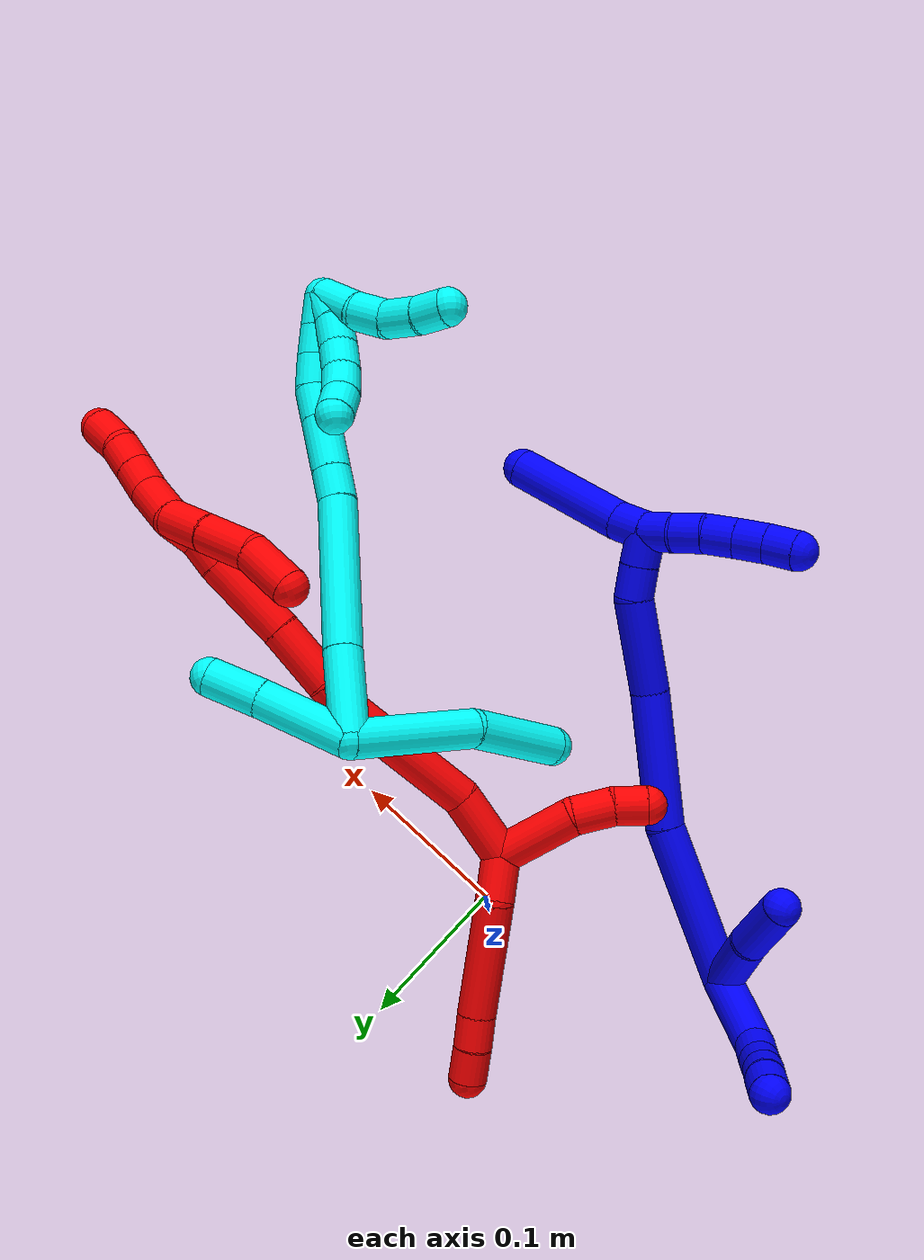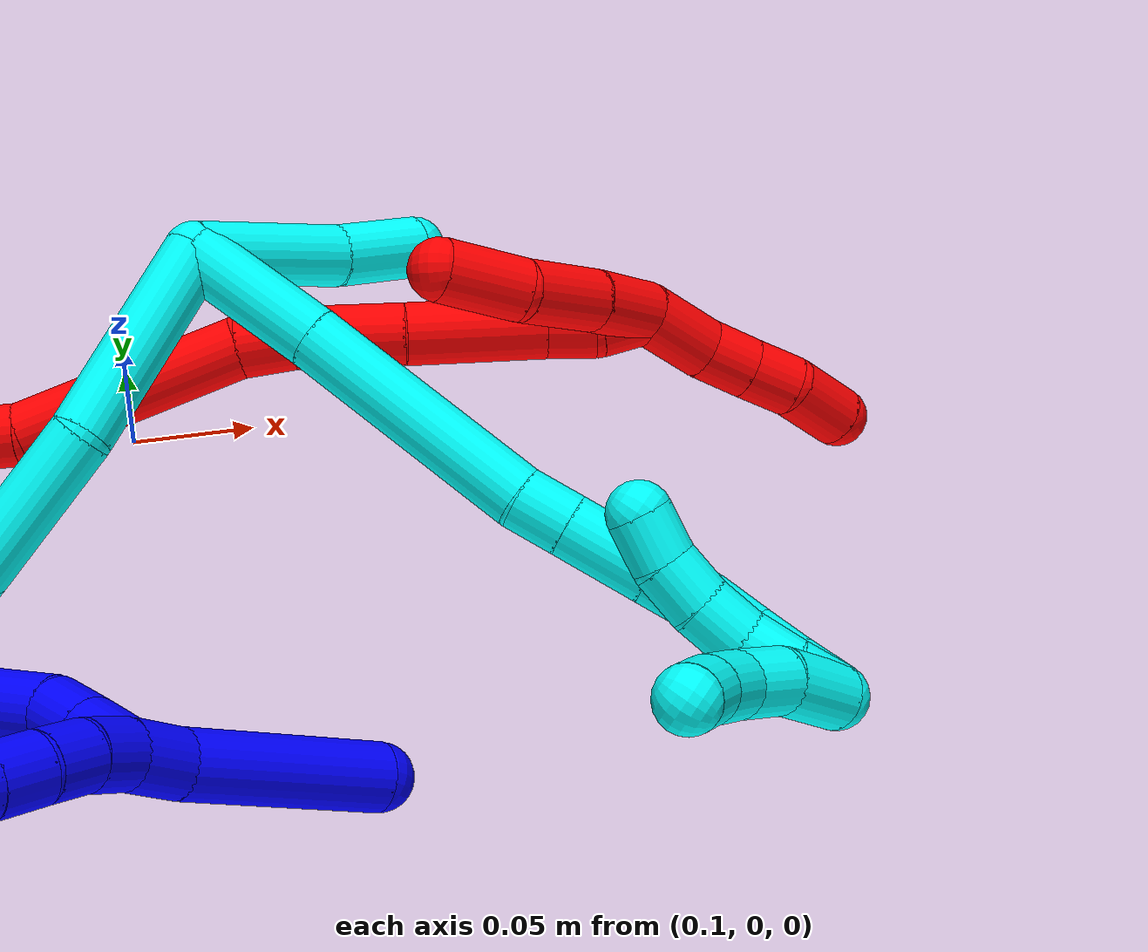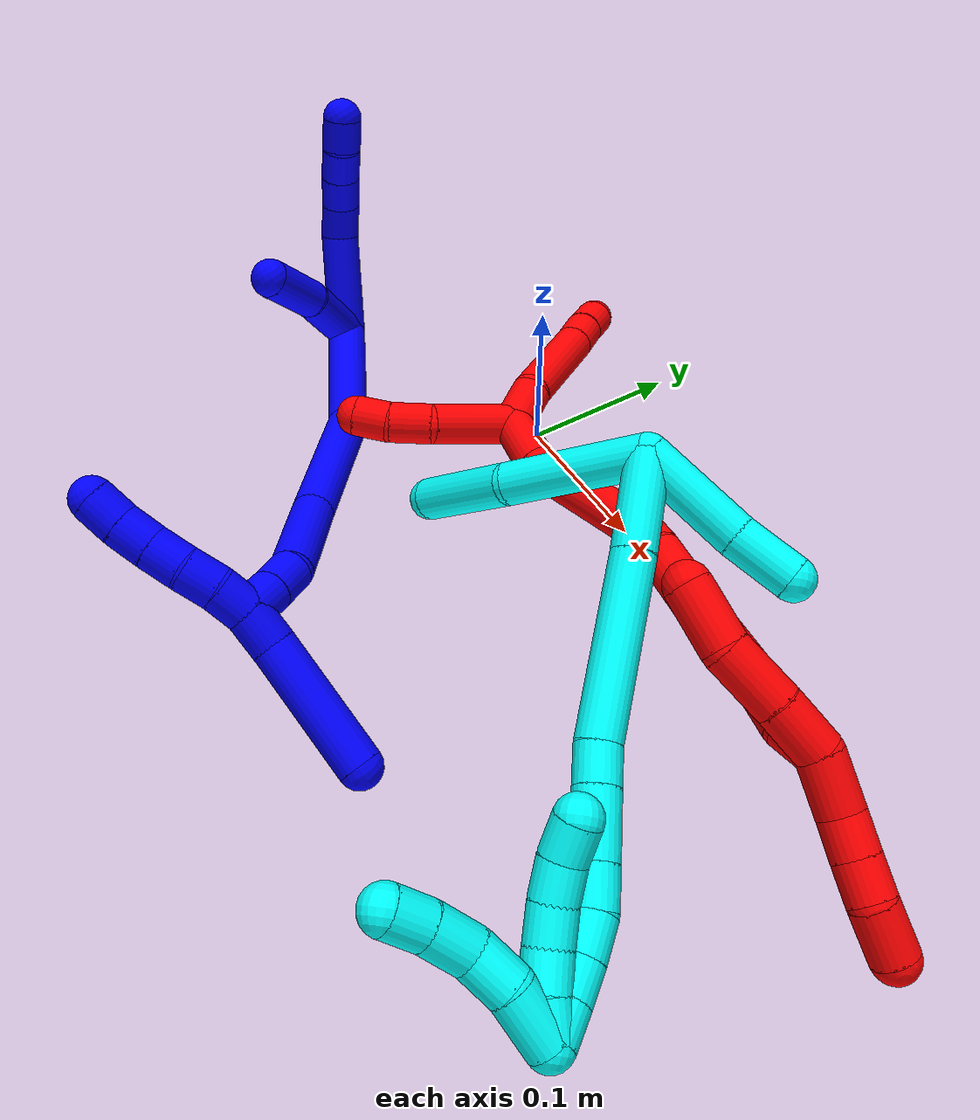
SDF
<sdf version="1.7">
 <world name="default">
  <plugin name="TubeGeneratorPlugin" filename="libtube_generator_plugin.so"/>
  <model name="photoneo_s_sensor">
   <static>1</static>
   <pose>0 0 2 1.57079 1.57079 3.14159</pose>
   <link name="link">
    <inertial><mass>0.1</mass></inertial>
    <sensor name="sensor" type="depth">
     <update_rate>30</update_rate>
     <camera>
      <horizontal_fov>1.22</horizontal_fov>
      <image><width>1920</width><height>1200</height><format>B8G8R8</format></image>
      <clip><near>0.1</near><far>4</far></clip>
      <depth_camera><output>points</output></depth_camera>
     </camera>
     <plugin name="camera_plugin" filename="libgazebo_ros_depth_camera.so">
      <baseline>0.2</baseline>
      <alwaysOn>1</alwaysOn>
      <updateRate>0.0</updateRate>
      <cameraName>camera_ir</cameraName>
      <imageTopicName>/camera/color/image_raw</imageTopicName>
      <cameraInfoTopicName>/camera/color/camera_info</cameraInfoTopicName>
      <depthImageTopicName>/camera/depth/image_raw</depthImageTopicName>
      <depthImageCameraInfoTopicName>/camera/depth/camera_info</depthImageCameraInfoTopicName>
      <pointCloudTopicName>/camera/depth/points</pointCloudTopicName>
      <frameName>fr_optical</frameName>
      <pointCloudCutoff>0.1</pointCloudCutoff>
      <pointCloudCutoffMax>2.0</pointCloudCutoffMax>
      <distortionK1>0</distortionK1>
      <distortionK2>0</distortionK2>
      <distortionK3>0</distortionK3>
      <distortionT1>0</distortionT1>
      <distortionT2>0</distortionT2>
      <CxPrime>0</CxPrime>
      <Cx>0</Cx>
      <Cy>0</Cy>
      <focalLength>0</focalLength>
      <hackBaseline>0</hackBaseline>
     </plugin>
    </sensor>
   </link>
  </model>
  <gravity>0 0 -9.8</gravity>
  <magnetic_field>6e-06 2.3e-05 -4.2e-05</magnetic_field>
  <atmosphere type="adiabatic"/>
  <physics name="default_physics" default="0" type="ode">
   <max_step_size>0.003</max_step_size>
   <real_time_factor>1</real_time_factor>
   <real_time_update_rate>1000</real_time_update_rate>
   <max_contacts>10000</max_contacts>
   <ode>
    <solver>
     <type>quick</type>
     <iters>100</iters>
     <sor>1.3</sor>
     <use_dynamic_moi_rescaling>0</use_dynamic_moi_rescaling>
    </solver>
    <constraints>
     <contact_max_correcting_vel>0</contact_max_correcting_vel>
     <contact_surface_layer>0.001</contact_surface_layer>
     <cfm>0</cfm>
     <erp>0.2</erp>
    </constraints>
   </ode>
  </physics>
  <scene><ambient>0.4 0.4 0.4 1</ambient><background>0.7 0.7 0.7 1</background><shadows>0</shadows></scene>
  <audio><device>default</device></audio>
  <spherical_coordinates>
   <surface_model>EARTH_WGS84</surface_model>
   <latitude_deg>0</latitude_deg>
   <longitude_deg>0</longitude_deg>
   <elevation>0</elevation>
   <heading_deg>0</heading_deg>
  </spherical_coordinates>
  <model name="bin">
   <static>1</static>
   <link name="bottom">
    <collision name="collision-bottom">
     <pose>0 0 -0.01 0 -0 0</pose>
     <geometry><box><size>0.8 0.6 0.02</size></box></geometry>
     <surface>
      <friction><ode><mu>100</mu><mu2>100</mu2></ode></friction>
      <contact><collide_bitmask>65535</collide_bitmask></contact>
     </surface>
    </collision>
   </link>
   <link name="west_wall">
    <collision name="collision-west_wall">
     <pose>-0.41 0 0.1 0 -0 0</pose>
     <geometry><box><size>0.02 0.6 0.2</size></box></geometry>
     <surface>
      <friction><ode><mu>100</mu><mu2>100</mu2></ode></friction>
      <contact><collide_bitmask>65535</collide_bitmask></contact>
     </surface>
    </collision>
   </link>
   <link name="east_wall">
    <collision name="collision-east_wall">
     <pose>0.41 0 0.1 0 -0 0</pose>
     <geometry><box><size>0.02 0.6 0.2</size></box></geometry>
     <surface>
      <friction><ode><mu>100</mu><mu2>100</mu2></ode></friction>
      <contact><collide_bitmask>65535</collide_bitmask></contact>
     </surface>
    </collision>
   </link>
   <link name="south_wall">
    <collision name="collision-south_wall">
     <pose>0 -0.31 0.1 0 -0 0</pose>
     <geometry><box><size>0.8 0.02 0.2</size></box></geometry>
     <surface>
      <friction><ode><mu>100</mu><mu2>100</mu2></ode></friction>
      <contact><collide_bitmask>65535</collide_bitmask></contact>
     </surface>
    </collision>
   </link>
   <link name="north_wall">
    <collision name="collision-north_wall">
     <pose>0 0.31 0.1 0 -0 0</pose>
     <geometry><box><size>0.8 0.02 0.2</size></box></geometry>
     <surface>
      <friction><ode><mu>100</mu><mu2>100</mu2></ode></friction>
      <contact><collide_bitmask>65535</collide_bitmask></contact>
     </surface>
    </collision>
   </link>
  </model>
  <model name="1">
   <static>0</static>
   <link name="1">
    <collision name="collision-cylinder-e_1_2_8">
     <pose>-0.00282 0.015648 0.0292 -0.491943 -0.084924 0.021333</pose>
     <geometry><cylinder><radius>0.0125</radius><length>0.066496</length></cylinder></geometry>
     <surface>
      <friction><ode><mu>1.16</mu><mu2>1.16</mu2><slip1>0</slip1><slip2>0</slip2></ode></friction>
      <contact><ode><kp>1e+06</kp><kd>1</kd><max_vel>0</max_vel><min_depth>0.001</min_depth></ode></contact>
     </surface>
    </collision>
    <visual name="visual-cylinder-e_1_2_8">
     <pose>-0.00282 0.015648 0.0292 -0.491943 -0.084924 0.021333</pose>
     <geometry><cylinder><radius>0.0125</radius><length>0.066496</length></cylinder></geometry>
     <material><ambient>0 0 1 1</ambient></material>
    </visual>
    <collision name="collision-cylinder-e_2_8_9">
     <pose>-0.00332 0.03777 0.067161 -0.636395 0.209853 -0.06935</pose>
     <geometry><cylinder><radius>0.0125</radius><length>0.022277</length></cylinder></geometry>
     <surface>
      <friction><ode><mu>1.16</mu><mu2>1.16</mu2><slip1>0</slip1><slip2>0</slip2></ode></friction>
      <contact><ode><kp>1e+06</kp><kd>1</kd><max_vel>0</max_vel><min_depth>0.001</min_depth></ode></contact>
     </surface>
    </collision>
    <visual name="visual-cylinder-e_2_8_9">
     <pose>-0.00332 0.03777 0.067161 -0.636395 0.209853 -0.06935</pose>
     <geometry><cylinder><radius>0.0125</radius><length>0.022277</length></cylinder></geometry>
     <material><ambient>0 0 1 1</ambient></material>
    </visual>
    <collision name="collision-cylinder-e_3_9_10">
     <pose>0.002634 0.049818 0.083753 -0.618627 0.361382 -0.116628</pose>
     <geometry><cylinder><radius>0.0125</radius><length>0.020552</length></cylinder></geometry>
     <surface>
      <friction><ode><mu>1.16</mu><mu2>1.16</mu2><slip1>0</slip1><slip2>0</slip2></ode></friction>
      <contact><ode><kp>1e+06</kp><kd>1</kd><max_vel>0</max_vel><min_depth>0.001</min_depth></ode></contact>
     </surface>
    </collision>
    <visual name="visual-cylinder-e_3_9_10">
     <pose>0.002634 0.049818 0.083753 -0.618627 0.361382 -0.116628</pose>
     <geometry><cylinder><radius>0.0125</radius><length>0.020552</length></cylinder></geometry>
     <material><ambient>0 0 1 1</ambient></material>
    </visual>
    <collision name="collision-cylinder-e_4_10_11">
     <pose>0.010067 0.061187 0.098924 -0.668201 0.386018 -0.135473</pose>
     <geometry><cylinder><radius>0.0125</radius><length>0.020188</length></cylinder></geometry>
     <surface>
      <friction><ode><mu>1.16</mu><mu2>1.16</mu2><slip1>0</slip1><slip2>0</slip2></ode></friction>
      <contact><ode><kp>1e+06</kp><kd>1</kd><max_vel>0</max_vel><min_depth>0.001</min_depth></ode></contact>
     </surface>
    </collision>
    <visual name="visual-cylinder-e_4_10_11">
     <pose>0.010067 0.061187 0.098924 -0.668201 0.386018 -0.135473</pose>
     <geometry><cylinder><radius>0.0125</radius><length>0.020188</length></cylinder></geometry>
     <material><ambient>0 0 1 1</ambient></material>
    </visual>
    <collision name="collision-cylinder-e_5_11_6">
     <pose>0.016096 0.072916 0.11431 -0.635616 0.219335 -0.072411</pose>
     <geometry><cylinder><radius>0.0125</radius><length>0.020487</length></cylinder></geometry>
     <surface>
      <friction><ode><mu>1.16</mu><mu2>1.16</mu2><slip1>0</slip1><slip2>0</slip2></ode></friction>
      <contact><ode><kp>1e+06</kp><kd>1</kd><max_vel>0</max_vel><min_depth>0.001</min_depth></ode></contact>
     </surface>
    </collision>
    <visual name="visual-cylinder-e_5_11_6">
     <pose>0.016096 0.072916 0.11431 -0.635616 0.219335 -0.072411</pose>
     <geometry><cylinder><radius>0.0125</radius><length>0.020487</length></cylinder></geometry>
     <material><ambient>0 0 1 1</ambient></material>
    </visual>
    <collision name="collision-cylinder-e_1_2_12">
     <pose>0.022729 0.000889 0.01773 -0.050076 0.907724 -0.024432</pose>
     <geometry><cylinder><radius>0.0125</radius><length>0.057681</length></cylinder></geometry>
     <surface>
      <friction><ode><mu>1.16</mu><mu2>1.16</mu2><slip1>0</slip1><slip2>0</slip2></ode></friction>
      <contact><ode><kp>1e+06</kp><kd>1</kd><max_vel>0</max_vel><min_depth>0.001</min_depth></ode></contact>
     </surface>
    </collision>
    <visual name="visual-cylinder-e_1_2_12">
     <pose>0.022729 0.000889 0.01773 -0.050076 0.907724 -0.024432</pose>
     <geometry><cylinder><radius>0.0125</radius><length>0.057681</length></cylinder></geometry>
     <material><ambient>0 0 1 1</ambient></material>
    </visual>
    <collision name="collision-cylinder-e_2_12_5">
     <pose>0.06142 -0.001735 0.0489 0.2556 0.854641 0.1169</pose>
     <geometry><cylinder><radius>0.0125</radius><length>0.042319</length></cylinder></geometry>
     <surface>
      <friction><ode><mu>1.16</mu><mu2>1.16</mu2><slip1>0</slip1><slip2>0</slip2></ode></friction>
      <contact><ode><kp>1e+06</kp><kd>1</kd><max_vel>0</max_vel><min_depth>0.001</min_depth></ode></contact>
     </surface>
    </collision>
    <visual name="visual-cylinder-e_2_12_5">
     <pose>0.06142 -0.001735 0.0489 0.2556 0.854641 0.1169</pose>
     <geometry><cylinder><radius>0.0125</radius><length>0.042319</length></cylinder></geometry>
     <material><ambient>0 0 1 1</ambient></material>
    </visual>
    <collision name="collision-cylinder-e_1_2_13">
     <pose>0.049563 -0.004602 -0.019825 2.91352 1.18116 2.80316</pose>
     <geometry><cylinder><radius>0.0125</radius><length>0.107158</length></cylinder></geometry>
     <surface>
      <friction><ode><mu>1.16</mu><mu2>1.16</mu2><slip1>0</slip1><slip2>0</slip2></ode></friction>
      <contact><ode><kp>1e+06</kp><kd>1</kd><max_vel>0</max_vel><min_depth>0.001</min_depth></ode></contact>
     </surface>
    </collision>
    <visual name="visual-cylinder-e_1_2_13">
     <pose>0.049563 -0.004602 -0.019825 2.91352 1.18116 2.80316</pose>
     <geometry><cylinder><radius>0.0125</radius><length>0.107158</length></cylinder></geometry>
     <material><ambient>0 0 1 1</ambient></material>
    </visual>
    <collision name="collision-cylinder-e_2_13_14">
     <pose>0.140036 -0.021629 -0.049759 2.25374 1.19759 1.92422</pose>
     <geometry><cylinder><radius>0.0125</radius><length>0.087868</length></cylinder></geometry>
     <surface>
      <friction><ode><mu>1.16</mu><mu2>1.16</mu2><slip1>0</slip1><slip2>0</slip2></ode></friction>
      <contact><ode><kp>1e+06</kp><kd>1</kd><max_vel>0</max_vel><min_depth>0.001</min_depth></ode></contact>
     </surface>
    </collision>
    <visual name="visual-cylinder-e_2_13_14">
     <pose>0.140036 -0.021629 -0.049759 2.25374 1.19759 1.92422</pose>
     <geometry><cylinder><radius>0.0125</radius><length>0.087868</length></cylinder></geometry>
     <material><ambient>0 0 1 1</ambient></material>
    </visual>
    <collision name="collision-cylinder-e_3_14_15">
     <pose>0.211394 -0.038209 -0.064162 2.37284 1.37706 2.22783</pose>
     <geometry><cylinder><radius>0.0125</radius><length>0.062058</length></cylinder></geometry>
     <surface>
      <friction><ode><mu>1.16</mu><mu2>1.16</mu2><slip1>0</slip1><slip2>0</slip2></ode></friction>
      <contact><ode><kp>1e+06</kp><kd>1</kd><max_vel>0</max_vel><min_depth>0.001</min_depth></ode></contact>
     </surface>
    </collision>
    <visual name="visual-cylinder-e_3_14_15">
     <pose>0.211394 -0.038209 -0.064162 2.37284 1.37706 2.22783</pose>
     <geometry><cylinder><radius>0.0125</radius><length>0.062058</length></cylinder></geometry>
     <material><ambient>0 0 1 1</ambient></material>
    </visual>
    <collision name="collision-cylinder-e_4_15_16">
     <pose>0.25159 -0.046948 -0.06816 1.50632 1.13021 1.07269</pose>
     <geometry><cylinder><radius>0.0125</radius><length>0.021553</length></cylinder></geometry>
     <surface>
      <friction><ode><mu>1.16</mu><mu2>1.16</mu2><slip1>0</slip1><slip2>0</slip2></ode></friction>
      <contact><ode><kp>1e+06</kp><kd>1</kd><max_vel>0</max_vel><min_depth>0.001</min_depth></ode></contact>
     </surface>
    </collision>
    <visual name="visual-cylinder-e_4_15_16">
     <pose>0.25159 -0.046948 -0.06816 1.50632 1.13021 1.07269</pose>
     <geometry><cylinder><radius>0.0125</radius><length>0.021553</length></cylinder></geometry>
     <material><ambient>0 0 1 1</ambient></material>
    </visual>
    <collision name="collision-cylinder-e_5_16_1">
     <pose>0.270917 -0.056194 -0.067083 1.4047 1.1126 0.968844</pose>
     <geometry><cylinder><radius>0.0125</radius><length>0.021363</length></cylinder></geometry>
     <surface>
      <friction><ode><mu>1.16</mu><mu2>1.16</mu2><slip1>0</slip1><slip2>0</slip2></ode></friction>
      <contact><ode><kp>1e+06</kp><kd>1</kd><max_vel>0</max_vel><min_depth>0.001</min_depth></ode></contact>
     </surface>
    </collision>
    <visual name="visual-cylinder-e_5_16_1">
     <pose>0.270917 -0.056194 -0.067083 1.4047 1.1126 0.968844</pose>
     <geometry><cylinder><radius>0.0125</radius><length>0.021363</length></cylinder></geometry>
     <material><ambient>0 0 1 1</ambient></material>
    </visual>
    <collision name="collision-cylinder-e_1_1_17">
     <pose>0.282322 -0.059614 -0.077367 -3.03002 0.162485 -1.93926</pose>
     <geometry><cylinder><radius>0.0125</radius><length>0.022566</length></cylinder></geometry>
     <surface>
      <friction><ode><mu>1.16</mu><mu2>1.16</mu2><slip1>0</slip1><slip2>0</slip2></ode></friction>
      <contact><ode><kp>1e+06</kp><kd>1</kd><max_vel>0</max_vel><min_depth>0.001</min_depth></ode></contact>
     </surface>
    </collision>
    <visual name="visual-cylinder-e_1_1_17">
     <pose>0.282322 -0.059614 -0.077367 -3.03002 0.162485 -1.93926</pose>
     <geometry><cylinder><radius>0.0125</radius><length>0.022566</length></cylinder></geometry>
     <material><ambient>0 0 1 1</ambient></material>
    </visual>
    <collision name="collision-cylinder-e_2_17_4">
     <pose>0.298252 -0.052012 -0.123923 -2.96422 0.372876 -2.26057</pose>
     <geometry><cylinder><radius>0.0125</radius><length>0.077434</length></cylinder></geometry>
     <surface>
      <friction><ode><mu>1.16</mu><mu2>1.16</mu2><slip1>0</slip1><slip2>0</slip2></ode></friction>
      <contact><ode><kp>1e+06</kp><kd>1</kd><max_vel>0</max_vel><min_depth>0.001</min_depth></ode></contact>
     </surface>
    </collision>
    <visual name="visual-cylinder-e_2_17_4">
     <pose>0.298252 -0.052012 -0.123923 -2.96422 0.372876 -2.26057</pose>
     <geometry><cylinder><radius>0.0125</radius><length>0.077434</length></cylinder></geometry>
     <material><ambient>0 0 1 1</ambient></material>
    </visual>
    <collision name="collision-cylinder-e_1_1_18">
     <pose>0.28073 -0.063807 -0.056751 0.299871 0.02336 0.003529</pose>
     <geometry><cylinder><radius>0.0125</radius><length>0.02</length></cylinder></geometry>
     <surface>
      <friction><ode><mu>1.16</mu><mu2>1.16</mu2><slip1>0</slip1><slip2>0</slip2></ode></friction>
      <contact><ode><kp>1e+06</kp><kd>1</kd><max_vel>0</max_vel><min_depth>0.001</min_depth></ode></contact>
     </surface>
    </collision>
    <visual name="visual-cylinder-e_1_1_18">
     <pose>0.28073 -0.063807 -0.056751 0.299871 0.02336 0.003529</pose>
     <geometry><cylinder><radius>0.0125</radius><length>0.02</length></cylinder></geometry>
     <material><ambient>0 0 1 1</ambient></material>
    </visual>
    <collision name="collision-cylinder-e_2_18_19">
     <pose>0.280662 -0.071207 -0.038248 0.461079 -0.030191 -0.007087</pose>
     <geometry><cylinder><radius>0.0125</radius><length>0.02</length></cylinder></geometry>
     <surface>
      <friction><ode><mu>1.16</mu><mu2>1.16</mu2><slip1>0</slip1><slip2>0</slip2></ode></friction>
      <contact><ode><kp>1e+06</kp><kd>1</kd><max_vel>0</max_vel><min_depth>0.001</min_depth></ode></contact>
     </surface>
    </collision>
    <visual name="visual-cylinder-e_2_18_19">
     <pose>0.280662 -0.071207 -0.038248 0.461079 -0.030191 -0.007087</pose>
     <geometry><cylinder><radius>0.0125</radius><length>0.02</length></cylinder></geometry>
     <material><ambient>0 0 1 1</ambient></material>
    </visual>
    <collision name="collision-cylinder-e_3_19_20">
     <pose>0.278523 -0.080351 -0.020661 0.498205 -0.184792 -0.047134</pose>
     <geometry><cylinder><radius>0.0125</radius><length>0.02</length></cylinder></geometry>
     <surface>
      <friction><ode><mu>1.16</mu><mu2>1.16</mu2><slip1>0</slip1><slip2>0</slip2></ode></friction>
      <contact><ode><kp>1e+06</kp><kd>1</kd><max_vel>0</max_vel><min_depth>0.001</min_depth></ode></contact>
     </surface>
    </collision>
    <visual name="visual-cylinder-e_3_19_20">
     <pose>0.278523 -0.080351 -0.020661 0.498205 -0.184792 -0.047134</pose>
     <geometry><cylinder><radius>0.0125</radius><length>0.02</length></cylinder></geometry>
     <material><ambient>0 0 1 1</ambient></material>
    </visual>
    <collision name="collision-cylinder-e_4_20_21">
     <pose>0.274842 -0.089266 -0.003148 0.44345 -0.185437 -0.041917</pose>
     <geometry><cylinder><radius>0.0125</radius><length>0.02</length></cylinder></geometry>
     <surface>
      <friction><ode><mu>1.16</mu><mu2>1.16</mu2><slip1>0</slip1><slip2>0</slip2></ode></friction>
      <contact><ode><kp>1e+06</kp><kd>1</kd><max_vel>0</max_vel><min_depth>0.001</min_depth></ode></contact>
     </surface>
    </collision>
    <visual name="visual-cylinder-e_4_20_21">
     <pose>0.274842 -0.089266 -0.003148 0.44345 -0.185437 -0.041917</pose>
     <geometry><cylinder><radius>0.0125</radius><length>0.02</length></cylinder></geometry>
     <material><ambient>0 0 1 1</ambient></material>
    </visual>
    <collision name="collision-cylinder-e_5_21_3">
     <pose>0.271236 -0.096575 0.015075 0.319553 -0.177137 -0.028619</pose>
     <geometry><cylinder><radius>0.0125</radius><length>0.02</length></cylinder></geometry>
     <surface>
      <friction><ode><mu>1.16</mu><mu2>1.16</mu2><slip1>0</slip1><slip2>0</slip2></ode></friction>
      <contact><ode><kp>1e+06</kp><kd>1</kd><max_vel>0</max_vel><min_depth>0.001</min_depth></ode></contact>
     </surface>
    </collision>
    <visual name="visual-cylinder-e_5_21_3">
     <pose>0.271236 -0.096575 0.015075 0.319553 -0.177137 -0.028619</pose>
     <geometry><cylinder><radius>0.0125</radius><length>0.02</length></cylinder></geometry>
     <material><ambient>0 0 1 1</ambient></material>
    </visual>
    <collision name="collision-sphere-3">
     <pose>0.269473 -0.099667 0.02442 0 -0 0</pose>
     <geometry><sphere><radius>0.0125</radius></sphere></geometry>
     <surface>
      <friction><ode><mu>1.16</mu><mu2>1.16</mu2><slip1>0</slip1><slip2>0</slip2></ode></friction>
      <contact><ode><kp>1e+06</kp><kd>1</kd><max_vel>0</max_vel><min_depth>0.001</min_depth></ode></contact>
     </surface>
    </collision>
    <visual name="visual-sphere-3">
     <pose>0.269473 -0.099667 0.02442 0 -0 0</pose>
     <geometry><sphere><radius>0.0125</radius></sphere></geometry>
     <material><ambient>0 0 1 1</ambient></material>
    </visual>
    <collision name="collision-sphere-21">
     <pose>0.272998 -0.093483 0.005729 0 -0 0</pose>
     <geometry><sphere><radius>0.0125</radius></sphere></geometry>
     <surface>
      <friction><ode><mu>1.16</mu><mu2>1.16</mu2><slip1>0</slip1><slip2>0</slip2></ode></friction>
      <contact><ode><kp>1e+06</kp><kd>1</kd><max_vel>0</max_vel><min_depth>0.001</min_depth></ode></contact>
     </surface>
    </collision>
    <visual name="visual-sphere-21">
     <pose>0.272998 -0.093483 0.005729 0 -0 0</pose>
     <geometry><sphere><radius>0.0125</radius></sphere></geometry>
     <material><ambient>0 0 1 1</ambient></material>
    </visual>
    <collision name="collision-sphere-20">
     <pose>0.276685 -0.085049 -0.012026 0 -0 0</pose>
     <geometry><sphere><radius>0.0125</radius></sphere></geometry>
     <surface>
      <friction><ode><mu>1.16</mu><mu2>1.16</mu2><slip1>0</slip1><slip2>0</slip2></ode></friction>
      <contact><ode><kp>1e+06</kp><kd>1</kd><max_vel>0</max_vel><min_depth>0.001</min_depth></ode></contact>
     </surface>
    </collision>
    <visual name="visual-sphere-20">
     <pose>0.276685 -0.085049 -0.012026 0 -0 0</pose>
     <geometry><sphere><radius>0.0125</radius></sphere></geometry>
     <material><ambient>0 0 1 1</ambient></material>
    </visual>
    <collision name="collision-sphere-19">
     <pose>0.28036 -0.075654 -0.029296 0 -0 0</pose>
     <geometry><sphere><radius>0.0125</radius></sphere></geometry>
     <surface>
      <friction><ode><mu>1.16</mu><mu2>1.16</mu2><slip1>0</slip1><slip2>0</slip2></ode></friction>
      <contact><ode><kp>1e+06</kp><kd>1</kd><max_vel>0</max_vel><min_depth>0.001</min_depth></ode></contact>
     </surface>
    </collision>
    <visual name="visual-sphere-19">
     <pose>0.28036 -0.075654 -0.029296 0 -0 0</pose>
     <geometry><sphere><radius>0.0125</radius></sphere></geometry>
     <material><ambient>0 0 1 1</ambient></material>
    </visual>
    <collision name="collision-sphere-6">
     <pose>0.018325 0.078852 0.122356 0 -0 0</pose>
     <geometry><sphere><radius>0.0125</radius></sphere></geometry>
     <surface>
      <friction><ode><mu>1.16</mu><mu2>1.16</mu2><slip1>0</slip1><slip2>0</slip2></ode></friction>
      <contact><ode><kp>1e+06</kp><kd>1</kd><max_vel>0</max_vel><min_depth>0.001</min_depth></ode></contact>
     </surface>
    </collision>
    <visual name="visual-sphere-6">
     <pose>0.018325 0.078852 0.122356 0 -0 0</pose>
     <geometry><sphere><radius>0.0125</radius></sphere></geometry>
     <material><ambient>0 0 1 1</ambient></material>
    </visual>
    <collision name="collision-sphere-11">
     <pose>0.013868 0.06698 0.106264 0 -0 0</pose>
     <geometry><sphere><radius>0.0125</radius></sphere></geometry>
     <surface>
      <friction><ode><mu>1.16</mu><mu2>1.16</mu2><slip1>0</slip1><slip2>0</slip2></ode></friction>
      <contact><ode><kp>1e+06</kp><kd>1</kd><max_vel>0</max_vel><min_depth>0.001</min_depth></ode></contact>
     </surface>
    </collision>
    <visual name="visual-sphere-11">
     <pose>0.013868 0.06698 0.106264 0 -0 0</pose>
     <geometry><sphere><radius>0.0125</radius></sphere></geometry>
     <material><ambient>0 0 1 1</ambient></material>
    </visual>
    <collision name="collision-sphere-10">
     <pose>0.006267 0.055393 0.091584 0 -0 0</pose>
     <geometry><sphere><radius>0.0125</radius></sphere></geometry>
     <surface>
      <friction><ode><mu>1.16</mu><mu2>1.16</mu2><slip1>0</slip1><slip2>0</slip2></ode></friction>
      <contact><ode><kp>1e+06</kp><kd>1</kd><max_vel>0</max_vel><min_depth>0.001</min_depth></ode></contact>
     </surface>
    </collision>
    <visual name="visual-sphere-10">
     <pose>0.006267 0.055393 0.091584 0 -0 0</pose>
     <geometry><sphere><radius>0.0125</radius></sphere></geometry>
     <material><ambient>0 0 1 1</ambient></material>
    </visual>
    <collision name="collision-sphere-9">
     <pose>-0.001 0.044244 0.075922 0 -0 0</pose>
     <geometry><sphere><radius>0.0125</radius></sphere></geometry>
     <surface>
      <friction><ode><mu>1.16</mu><mu2>1.16</mu2><slip1>0</slip1><slip2>0</slip2></ode></friction>
      <contact><ode><kp>1e+06</kp><kd>1</kd><max_vel>0</max_vel><min_depth>0.001</min_depth></ode></contact>
     </surface>
    </collision>
    <visual name="visual-sphere-9">
     <pose>-0.001 0.044244 0.075922 0 -0 0</pose>
     <geometry><sphere><radius>0.0125</radius></sphere></geometry>
     <material><ambient>0 0 1 1</ambient></material>
    </visual>
    <collision name="collision-sphere-2">
     <geometry><sphere><radius>0.0125</radius></sphere></geometry>
     <surface>
      <friction><ode><mu>1.16</mu><mu2>1.16</mu2><slip1>0</slip1><slip2>0</slip2></ode></friction>
      <contact><ode><kp>1e+06</kp><kd>1</kd><max_vel>0</max_vel><min_depth>0.001</min_depth></ode></contact>
     </surface>
    </collision>
    <visual name="visual-sphere-2">
     <geometry><sphere><radius>0.0125</radius></sphere></geometry>
     <material><ambient>0 0 1 1</ambient></material>
    </visual>
    <collision name="collision-sphere-8">
     <pose>-0.00564 0.031295 0.058399 0 -0 0</pose>
     <geometry><sphere><radius>0.0125</radius></sphere></geometry>
     <surface>
      <friction><ode><mu>1.16</mu><mu2>1.16</mu2><slip1>0</slip1><slip2>0</slip2></ode></friction>
      <contact><ode><kp>1e+06</kp><kd>1</kd><max_vel>0</max_vel><min_depth>0.001</min_depth></ode></contact>
     </surface>
    </collision>
    <visual name="visual-sphere-8">
     <pose>-0.00564 0.031295 0.058399 0 -0 0</pose>
     <geometry><sphere><radius>0.0125</radius></sphere></geometry>
     <material><ambient>0 0 1 1</ambient></material>
    </visual>
    <collision name="collision-sphere-12">
     <pose>0.045459 0.001777 0.035461 0 -0 0</pose>
     <geometry><sphere><radius>0.0125</radius></sphere></geometry>
     <surface>
      <friction><ode><mu>1.16</mu><mu2>1.16</mu2><slip1>0</slip1><slip2>0</slip2></ode></friction>
      <contact><ode><kp>1e+06</kp><kd>1</kd><max_vel>0</max_vel><min_depth>0.001</min_depth></ode></contact>
     </surface>
    </collision>
    <visual name="visual-sphere-12">
     <pose>0.045459 0.001777 0.035461 0 -0 0</pose>
     <geometry><sphere><radius>0.0125</radius></sphere></geometry>
     <material><ambient>0 0 1 1</ambient></material>
    </visual>
    <collision name="collision-sphere-5">
     <pose>0.077381 -0.005247 0.06234 0 -0 0</pose>
     <geometry><sphere><radius>0.0125</radius></sphere></geometry>
     <surface>
      <friction><ode><mu>1.16</mu><mu2>1.16</mu2><slip1>0</slip1><slip2>0</slip2></ode></friction>
      <contact><ode><kp>1e+06</kp><kd>1</kd><max_vel>0</max_vel><min_depth>0.001</min_depth></ode></contact>
     </surface>
    </collision>
    <visual name="visual-sphere-5">
     <pose>0.077381 -0.005247 0.06234 0 -0 0</pose>
     <geometry><sphere><radius>0.0125</radius></sphere></geometry>
     <material><ambient>0 0 1 1</ambient></material>
    </visual>
    <collision name="collision-sphere-13">
     <pose>0.099126 -0.009203 -0.03965 0 -0 0</pose>
     <geometry><sphere><radius>0.0125</radius></sphere></geometry>
     <surface>
      <friction><ode><mu>1.16</mu><mu2>1.16</mu2><slip1>0</slip1><slip2>0</slip2></ode></friction>
      <contact><ode><kp>1e+06</kp><kd>1</kd><max_vel>0</max_vel><min_depth>0.001</min_depth></ode></contact>
     </surface>
    </collision>
    <visual name="visual-sphere-13">
     <pose>0.099126 -0.009203 -0.03965 0 -0 0</pose>
     <geometry><sphere><radius>0.0125</radius></sphere></geometry>
     <material><ambient>0 0 1 1</ambient></material>
    </visual>
    <collision name="collision-sphere-14">
     <pose>0.180946 -0.034055 -0.059869 0 -0 0</pose>
     <geometry><sphere><radius>0.0125</radius></sphere></geometry>
     <surface>
      <friction><ode><mu>1.16</mu><mu2>1.16</mu2><slip1>0</slip1><slip2>0</slip2></ode></friction>
      <contact><ode><kp>1e+06</kp><kd>1</kd><max_vel>0</max_vel><min_depth>0.001</min_depth></ode></contact>
     </surface>
    </collision>
    <visual name="visual-sphere-14">
     <pose>0.180946 -0.034055 -0.059869 0 -0 0</pose>
     <geometry><sphere><radius>0.0125</radius></sphere></geometry>
     <material><ambient>0 0 1 1</ambient></material>
    </visual>
    <collision name="collision-sphere-15">
     <pose>0.241843 -0.042362 -0.068456 0 -0 0</pose>
     <geometry><sphere><radius>0.0125</radius></sphere></geometry>
     <surface>
      <friction><ode><mu>1.16</mu><mu2>1.16</mu2><slip1>0</slip1><slip2>0</slip2></ode></friction>
      <contact><ode><kp>1e+06</kp><kd>1</kd><max_vel>0</max_vel><min_depth>0.001</min_depth></ode></contact>
     </surface>
    </collision>
    <visual name="visual-sphere-15">
     <pose>0.241843 -0.042362 -0.068456 0 -0 0</pose>
     <geometry><sphere><radius>0.0125</radius></sphere></geometry>
     <material><ambient>0 0 1 1</ambient></material>
    </visual>
    <collision name="collision-sphere-16">
     <pose>0.261337 -0.051534 -0.067864 0 -0 0</pose>
     <geometry><sphere><radius>0.0125</radius></sphere></geometry>
     <surface>
      <friction><ode><mu>1.16</mu><mu2>1.16</mu2><slip1>0</slip1><slip2>0</slip2></ode></friction>
      <contact><ode><kp>1e+06</kp><kd>1</kd><max_vel>0</max_vel><min_depth>0.001</min_depth></ode></contact>
     </surface>
    </collision>
    <visual name="visual-sphere-16">
     <pose>0.261337 -0.051534 -0.067864 0 -0 0</pose>
     <geometry><sphere><radius>0.0125</radius></sphere></geometry>
     <material><ambient>0 0 1 1</ambient></material>
    </visual>
    <collision name="collision-sphere-1">
     <pose>0.280497 -0.060854 -0.066302 0 -0 0</pose>
     <geometry><sphere><radius>0.0125</radius></sphere></geometry>
     <surface>
      <friction><ode><mu>1.16</mu><mu2>1.16</mu2><slip1>0</slip1><slip2>0</slip2></ode></friction>
      <contact><ode><kp>1e+06</kp><kd>1</kd><max_vel>0</max_vel><min_depth>0.001</min_depth></ode></contact>
     </surface>
    </collision>
    <visual name="visual-sphere-1">
     <pose>0.280497 -0.060854 -0.066302 0 -0 0</pose>
     <geometry><sphere><radius>0.0125</radius></sphere></geometry>
     <material><ambient>0 0 1 1</ambient></material>
    </visual>
    <collision name="collision-sphere-18">
     <pose>0.280964 -0.06676 -0.047199 0 -0 0</pose>
     <geometry><sphere><radius>0.0125</radius></sphere></geometry>
     <surface>
      <friction><ode><mu>1.16</mu><mu2>1.16</mu2><slip1>0</slip1><slip2>0</slip2></ode></friction>
      <contact><ode><kp>1e+06</kp><kd>1</kd><max_vel>0</max_vel><min_depth>0.001</min_depth></ode></contact>
     </surface>
    </collision>
    <visual name="visual-sphere-18">
     <pose>0.280964 -0.06676 -0.047199 0 -0 0</pose>
     <geometry><sphere><radius>0.0125</radius></sphere></geometry>
     <material><ambient>0 0 1 1</ambient></material>
    </visual>
    <collision name="collision-sphere-17">
     <pose>0.284147 -0.058374 -0.088432 0 -0 0</pose>
     <geometry><sphere><radius>0.0125</radius></sphere></geometry>
     <surface>
      <friction><ode><mu>1.16</mu><mu2>1.16</mu2><slip1>0</slip1><slip2>0</slip2></ode></friction>
      <contact><ode><kp>1e+06</kp><kd>1</kd><max_vel>0</max_vel><min_depth>0.001</min_depth></ode></contact>
     </surface>
    </collision>
    <visual name="visual-sphere-17">
     <pose>0.284147 -0.058374 -0.088432 0 -0 0</pose>
     <geometry><sphere><radius>0.0125</radius></sphere></geometry>
     <material><ambient>0 0 1 1</ambient></material>
    </visual>
    <collision name="collision-sphere-4">
     <pose>0.312356 -0.04565 -0.159414 0 -0 0</pose>
     <geometry><sphere><radius>0.0125</radius></sphere></geometry>
     <surface>
      <friction><ode><mu>1.16</mu><mu2>1.16</mu2><slip1>0</slip1><slip2>0</slip2></ode></friction>
      <contact><ode><kp>1e+06</kp><kd>1</kd><max_vel>0</max_vel><min_depth>0.001</min_depth></ode></contact>
     </surface>
    </collision>
    <visual name="visual-sphere-4">
     <pose>0.312356 -0.04565 -0.159414 0 -0 0</pose>
     <geometry><sphere><radius>0.0125</radius></sphere></geometry>
     <material><ambient>0 0 1 1</ambient></material>
    </visual>
    <inertial>
     <pose>0.137821 -0.019682 -0.018942 0 -0 0</pose>
     <mass>0.75</mass>
     <inertia>
      <ixx>2.2e-05</ixx>
      <ixy>0</ixy>
      <ixz>0</ixz>
      <iyy>0.000281</iyy>
      <iyz>0</iyz>
      <izz>-0.000194</izz>
     </inertia>
    </inertial>
   </link>
   <pose>-0.147697 -0.064169 0.011495 0.566396 -0.470894 -0.586285</pose>
  </model>
  <model name="2">
   <static>0</static>
   <link name="2">
    <collision name="collision-cylinder-e_1_2_8">
     <pose>-0.003464 0.008222 -0.012033 -2.54219 -0.233328 0.725009</pose>
     <geometry><cylinder><radius>0.0125</radius><length>0.02996</length></cylinder></geometry>
     <surface>
      <friction><ode><mu>1.16</mu><mu2>1.16</mu2><slip1>0</slip1><slip2>0</slip2></ode></friction>
      <contact><ode><kp>1e+06</kp><kd>1</kd><max_vel>0</max_vel><min_depth>0.001</min_depth></ode></contact>
     </surface>
    </collision>
    <visual name="visual-cylinder-e_1_2_8">
     <pose>-0.003464 0.008222 -0.012033 -2.54219 -0.233328 0.725009</pose>
     <geometry><cylinder><radius>0.0125</radius><length>0.02996</length></cylinder></geometry>
     <material><ambient>1 0 0 1</ambient></material>
    </visual>
    <collision name="collision-cylinder-e_2_8_9">
     <pose>-0.003653 0.035432 -0.056765 -2.61549 0.086389 -0.318287</pose>
     <geometry><cylinder><radius>0.0125</radius><length>0.075907</length></cylinder></geometry>
     <surface>
      <friction><ode><mu>1.16</mu><mu2>1.16</mu2><slip1>0</slip1><slip2>0</slip2></ode></friction>
      <contact><ode><kp>1e+06</kp><kd>1</kd><max_vel>0</max_vel><min_depth>0.001</min_depth></ode></contact>
     </surface>
    </collision>
    <visual name="visual-cylinder-e_2_8_9">
     <pose>-0.003653 0.035432 -0.056765 -2.61549 0.086389 -0.318287</pose>
     <geometry><cylinder><radius>0.0125</radius><length>0.075907</length></cylinder></geometry>
     <material><ambient>1 0 0 1</ambient></material>
    </visual>
    <collision name="collision-cylinder-e_3_9_10">
     <pose>-6.1e-05 0.059768 -0.099066 -2.63338 0.028816 -0.110845</pose>
     <geometry><cylinder><radius>0.0125</radius><length>0.021992</length></cylinder></geometry>
     <surface>
      <friction><ode><mu>1.16</mu><mu2>1.16</mu2><slip1>0</slip1><slip2>0</slip2></ode></friction>
      <contact><ode><kp>1e+06</kp><kd>1</kd><max_vel>0</max_vel><min_depth>0.001</min_depth></ode></contact>
     </surface>
    </collision>
    <visual name="visual-cylinder-e_3_9_10">
     <pose>-6.1e-05 0.059768 -0.099066 -2.63338 0.028816 -0.110845</pose>
     <geometry><cylinder><radius>0.0125</radius><length>0.021992</length></cylinder></geometry>
     <material><ambient>1 0 0 1</ambient></material>
    </visual>
    <collision name="collision-cylinder-e_4_10_6">
     <pose>0.001518 0.07056 -0.118226 -2.62384 0.114247 -0.425351</pose>
     <geometry><cylinder><radius>0.0125</radius><length>0.022141</length></cylinder></geometry>
     <surface>
      <friction><ode><mu>1.16</mu><mu2>1.16</mu2><slip1>0</slip1><slip2>0</slip2></ode></friction>
      <contact><ode><kp>1e+06</kp><kd>1</kd><max_vel>0</max_vel><min_depth>0.001</min_depth></ode></contact>
     </surface>
    </collision>
    <visual name="visual-cylinder-e_4_10_6">
     <pose>0.001518 0.07056 -0.118226 -2.62384 0.114247 -0.425351</pose>
     <geometry><cylinder><radius>0.0125</radius><length>0.022141</length></cylinder></geometry>
     <material><ambient>1 0 0 1</ambient></material>
    </visual>
    <collision name="collision-cylinder-e_1_2_11">
     <pose>-0.008066 -0.024706 0.003994 1.41053 -0.311789 -0.266027</pose>
     <geometry><cylinder><radius>0.0125</radius><length>0.052589</length></cylinder></geometry>
     <surface>
      <friction><ode><mu>1.16</mu><mu2>1.16</mu2><slip1>0</slip1><slip2>0</slip2></ode></friction>
      <contact><ode><kp>1e+06</kp><kd>1</kd><max_vel>0</max_vel><min_depth>0.001</min_depth></ode></contact>
     </surface>
    </collision>
    <visual name="visual-cylinder-e_1_2_11">
     <pose>-0.008066 -0.024706 0.003994 1.41053 -0.311789 -0.266027</pose>
     <geometry><cylinder><radius>0.0125</radius><length>0.052589</length></cylinder></geometry>
     <material><ambient>1 0 0 1</ambient></material>
    </visual>
    <collision name="collision-cylinder-e_2_11_12">
     <pose>-0.018524 -0.062089 0.006071 1.72086 -0.184392 -0.214156</pose>
     <geometry><cylinder><radius>0.0125</radius><length>0.026084</length></cylinder></geometry>
     <surface>
      <friction><ode><mu>1.16</mu><mu2>1.16</mu2><slip1>0</slip1><slip2>0</slip2></ode></friction>
      <contact><ode><kp>1e+06</kp><kd>1</kd><max_vel>0</max_vel><min_depth>0.001</min_depth></ode></contact>
     </surface>
    </collision>
    <visual name="visual-cylinder-e_2_11_12">
     <pose>-0.018524 -0.062089 0.006071 1.72086 -0.184392 -0.214156</pose>
     <geometry><cylinder><radius>0.0125</radius><length>0.026084</length></cylinder></geometry>
     <material><ambient>1 0 0 1</ambient></material>
    </visual>
    <collision name="collision-cylinder-e_3_12_5">
     <pose>-0.023361 -0.084442 0.0004 1.94085 -0.231503 -0.336426</pose>
     <geometry><cylinder><radius>0.0125</radius><length>0.021327</length></cylinder></geometry>
     <surface>
      <friction><ode><mu>1.16</mu><mu2>1.16</mu2><slip1>0</slip1><slip2>0</slip2></ode></friction>
      <contact><ode><kp>1e+06</kp><kd>1</kd><max_vel>0</max_vel><min_depth>0.001</min_depth></ode></contact>
     </surface>
    </collision>
    <visual name="visual-cylinder-e_3_12_5">
     <pose>-0.023361 -0.084442 0.0004 1.94085 -0.231503 -0.336426</pose>
     <geometry><cylinder><radius>0.0125</radius><length>0.021327</length></cylinder></geometry>
     <material><ambient>1 0 0 1</ambient></material>
    </visual>
    <collision name="collision-cylinder-e_1_2_13">
     <pose>0.002778 0.004307 0.021874 -0.194431 0.123977 -0.012106</pose>
     <geometry><cylinder><radius>0.0125</radius><length>0.044933</length></cylinder></geometry>
     <surface>
      <friction><ode><mu>1.16</mu><mu2>1.16</mu2><slip1>0</slip1><slip2>0</slip2></ode></friction>
      <contact><ode><kp>1e+06</kp><kd>1</kd><max_vel>0</max_vel><min_depth>0.001</min_depth></ode></contact>
     </surface>
    </collision>
    <visual name="visual-cylinder-e_1_2_13">
     <pose>0.002778 0.004307 0.021874 -0.194431 0.123977 -0.012106</pose>
     <geometry><cylinder><radius>0.0125</radius><length>0.044933</length></cylinder></geometry>
     <material><ambient>1 0 0 1</ambient></material>
    </visual>
    <collision name="collision-cylinder-e_2_13_14">
     <pose>0.005301 0.030107 0.084369 -0.486651 -0.005558 0.00138</pose>
     <geometry><cylinder><radius>0.0125</radius><length>0.091914</length></cylinder></geometry>
     <surface>
      <friction><ode><mu>1.16</mu><mu2>1.16</mu2><slip1>0</slip1><slip2>0</slip2></ode></friction>
      <contact><ode><kp>1e+06</kp><kd>1</kd><max_vel>0</max_vel><min_depth>0.001</min_depth></ode></contact>
     </surface>
    </collision>
    <visual name="visual-cylinder-e_2_13_14">
     <pose>0.005301 0.030107 0.084369 -0.486651 -0.005558 0.00138</pose>
     <geometry><cylinder><radius>0.0125</radius><length>0.091914</length></cylinder></geometry>
     <material><ambient>1 0 0 1</ambient></material>
    </visual>
    <collision name="collision-cylinder-e_3_14_15">
     <pose>0.006473 0.054978 0.135555 -0.309492 0.127968 -0.019989</pose>
     <geometry><cylinder><radius>0.0125</radius><length>0.022366</length></cylinder></geometry>
     <surface>
      <friction><ode><mu>1.16</mu><mu2>1.16</mu2><slip1>0</slip1><slip2>0</slip2></ode></friction>
      <contact><ode><kp>1e+06</kp><kd>1</kd><max_vel>0</max_vel><min_depth>0.001</min_depth></ode></contact>
     </surface>
    </collision>
    <visual name="visual-cylinder-e_3_14_15">
     <pose>0.006473 0.054978 0.135555 -0.309492 0.127968 -0.019989</pose>
     <geometry><cylinder><radius>0.0125</radius><length>0.022366</length></cylinder></geometry>
     <material><ambient>1 0 0 1</ambient></material>
    </visual>
    <collision name="collision-cylinder-e_4_15_16">
     <pose>0.013735 0.064149 0.166214 -0.280694 0.272092 -0.038674</pose>
     <geometry><cylinder><radius>0.0125</radius><length>0.043423</length></cylinder></geometry>
     <surface>
      <friction><ode><mu>1.16</mu><mu2>1.16</mu2><slip1>0</slip1><slip2>0</slip2></ode></friction>
      <contact><ode><kp>1e+06</kp><kd>1</kd><max_vel>0</max_vel><min_depth>0.001</min_depth></ode></contact>
     </surface>
    </collision>
    <visual name="visual-cylinder-e_4_15_16">
     <pose>0.013735 0.064149 0.166214 -0.280694 0.272092 -0.038674</pose>
     <geometry><cylinder><radius>0.0125</radius><length>0.043423</length></cylinder></geometry>
     <material><ambient>1 0 0 1</ambient></material>
    </visual>
    <collision name="collision-cylinder-e_5_16_17">
     <pose>0.028047 0.078935 0.211486 -0.343038 0.307044 -0.053595</pose>
     <geometry><cylinder><radius>0.0125</radius><length>0.056095</length></cylinder></geometry>
     <surface>
      <friction><ode><mu>1.16</mu><mu2>1.16</mu2><slip1>0</slip1><slip2>0</slip2></ode></friction>
      <contact><ode><kp>1e+06</kp><kd>1</kd><max_vel>0</max_vel><min_depth>0.001</min_depth></ode></contact>
     </surface>
    </collision>
    <visual name="visual-cylinder-e_5_16_17">
     <pose>0.028047 0.078935 0.211486 -0.343038 0.307044 -0.053595</pose>
     <geometry><cylinder><radius>0.0125</radius><length>0.056095</length></cylinder></geometry>
     <material><ambient>1 0 0 1</ambient></material>
    </visual>
    <collision name="collision-cylinder-e_6_17_18">
     <pose>0.039087 0.090052 0.246121 -0.220925 0.258537 -0.028834</pose>
     <geometry><cylinder><radius>0.0125</radius><length>0.02005</length></cylinder></geometry>
     <surface>
      <friction><ode><mu>1.16</mu><mu2>1.16</mu2><slip1>0</slip1><slip2>0</slip2></ode></friction>
      <contact><ode><kp>1e+06</kp><kd>1</kd><max_vel>0</max_vel><min_depth>0.001</min_depth></ode></contact>
     </surface>
    </collision>
    <visual name="visual-cylinder-e_6_17_18">
     <pose>0.039087 0.090052 0.246121 -0.220925 0.258537 -0.028834</pose>
     <geometry><cylinder><radius>0.0125</radius><length>0.02005</length></cylinder></geometry>
     <material><ambient>1 0 0 1</ambient></material>
    </visual>
    <collision name="collision-cylinder-e_7_18_1">
     <pose>0.043357 0.097417 0.264641 -0.524323 0.161618 -0.043456</pose>
     <geometry><cylinder><radius>0.0125</radius><length>0.021218</length></cylinder></geometry>
     <surface>
      <friction><ode><mu>1.16</mu><mu2>1.16</mu2><slip1>0</slip1><slip2>0</slip2></ode></friction>
      <contact><ode><kp>1e+06</kp><kd>1</kd><max_vel>0</max_vel><min_depth>0.001</min_depth></ode></contact>
     </surface>
    </collision>
    <visual name="visual-cylinder-e_7_18_1">
     <pose>0.043357 0.097417 0.264641 -0.524323 0.161618 -0.043456</pose>
     <geometry><cylinder><radius>0.0125</radius><length>0.021218</length></cylinder></geometry>
     <material><ambient>1 0 0 1</ambient></material>
    </visual>
    <collision name="collision-cylinder-e_1_1_19">
     <pose>0.034406 0.095288 0.266537 2.34227 -0.803334 -1.57638</pose>
     <geometry><cylinder><radius>0.0125</radius><length>0.029619</length></cylinder></geometry>
     <surface>
      <friction><ode><mu>1.16</mu><mu2>1.16</mu2><slip1>0</slip1><slip2>0</slip2></ode></friction>
      <contact><ode><kp>1e+06</kp><kd>1</kd><max_vel>0</max_vel><min_depth>0.001</min_depth></ode></contact>
     </surface>
    </collision>
    <visual name="visual-cylinder-e_1_1_19">
     <pose>0.034406 0.095288 0.266537 2.34227 -0.803334 -1.57638</pose>
     <geometry><cylinder><radius>0.0125</radius><length>0.029619</length></cylinder></geometry>
     <material><ambient>1 0 0 1</ambient></material>
    </visual>
    <collision name="collision-cylinder-e_2_19_20">
     <pose>0.011781 0.078471 0.249994 2.35238 -0.732447 -1.48853</pose>
     <geometry><cylinder><radius>0.0125</radius><length>0.035795</length></cylinder></geometry>
     <surface>
      <friction><ode><mu>1.16</mu><mu2>1.16</mu2><slip1>0</slip1><slip2>0</slip2></ode></friction>
      <contact><ode><kp>1e+06</kp><kd>1</kd><max_vel>0</max_vel><min_depth>0.001</min_depth></ode></contact>
     </surface>
    </collision>
    <visual name="visual-cylinder-e_2_19_20">
     <pose>0.011781 0.078471 0.249994 2.35238 -0.732447 -1.48853</pose>
     <geometry><cylinder><radius>0.0125</radius><length>0.035795</length></cylinder></geometry>
     <material><ambient>1 0 0 1</ambient></material>
    </visual>
    <collision name="collision-cylinder-e_3_20_4">
     <pose>-0.011106 0.063832 0.228256 2.74391 -0.683341 -2.11054</pose>
     <geometry><cylinder><radius>0.0125</radius><length>0.034586</length></cylinder></geometry>
     <surface>
      <friction><ode><mu>1.16</mu><mu2>1.16</mu2><slip1>0</slip1><slip2>0</slip2></ode></friction>
      <contact><ode><kp>1e+06</kp><kd>1</kd><max_vel>0</max_vel><min_depth>0.001</min_depth></ode></contact>
     </surface>
    </collision>
    <visual name="visual-cylinder-e_3_20_4">
     <pose>-0.011106 0.063832 0.228256 2.74391 -0.683341 -2.11054</pose>
     <geometry><cylinder><radius>0.0125</radius><length>0.034586</length></cylinder></geometry>
     <material><ambient>1 0 0 1</ambient></material>
    </visual>
    <collision name="collision-cylinder-e_1_1_21">
     <pose>0.057346 0.104742 0.282457 -0.233641 0.938628 -0.118882</pose>
     <geometry><cylinder><radius>0.0125</radius><length>0.030448</length></cylinder></geometry>
     <surface>
      <friction><ode><mu>1.16</mu><mu2>1.16</mu2><slip1>0</slip1><slip2>0</slip2></ode></friction>
      <contact><ode><kp>1e+06</kp><kd>1</kd><max_vel>0</max_vel><min_depth>0.001</min_depth></ode></contact>
     </surface>
    </collision>
    <visual name="visual-cylinder-e_1_1_21">
     <pose>0.057346 0.104742 0.282457 -0.233641 0.938628 -0.118882</pose>
     <geometry><cylinder><radius>0.0125</radius><length>0.030448</length></cylinder></geometry>
     <material><ambient>1 0 0 1</ambient></material>
    </visual>
    <collision name="collision-cylinder-e_2_21_22">
     <pose>0.076585 0.10772 0.298877 -0.116168 0.73338 -0.044658</pose>
     <geometry><cylinder><radius>0.0125</radius><length>0.020787</length></cylinder></geometry>
     <surface>
      <friction><ode><mu>1.16</mu><mu2>1.16</mu2><slip1>0</slip1><slip2>0</slip2></ode></friction>
      <contact><ode><kp>1e+06</kp><kd>1</kd><max_vel>0</max_vel><min_depth>0.001</min_depth></ode></contact>
     </surface>
    </collision>
    <visual name="visual-cylinder-e_2_21_22">
     <pose>0.076585 0.10772 0.298877 -0.116168 0.73338 -0.044658</pose>
     <geometry><cylinder><radius>0.0125</radius><length>0.020787</length></cylinder></geometry>
     <material><ambient>1 0 0 1</ambient></material>
    </visual>
    <collision name="collision-cylinder-e_3_22_23">
     <pose>0.090237 0.109617 0.314206 -0.130165 0.714019 -0.04861</pose>
     <geometry><cylinder><radius>0.0125</radius><length>0.020443</length></cylinder></geometry>
     <surface>
      <friction><ode><mu>1.16</mu><mu2>1.16</mu2><slip1>0</slip1><slip2>0</slip2></ode></friction>
      <contact><ode><kp>1e+06</kp><kd>1</kd><max_vel>0</max_vel><min_depth>0.001</min_depth></ode></contact>
     </surface>
    </collision>
    <visual name="visual-cylinder-e_3_22_23">
     <pose>0.090237 0.109617 0.314206 -0.130165 0.714019 -0.04861</pose>
     <geometry><cylinder><radius>0.0125</radius><length>0.020443</length></cylinder></geometry>
     <material><ambient>1 0 0 1</ambient></material>
    </visual>
    <collision name="collision-cylinder-e_4_23_3">
     <pose>0.108818 0.113401 0.329042 -0.369666 0.996243 -0.202673</pose>
     <geometry><cylinder><radius>0.0125</radius><length>0.028322</length></cylinder></geometry>
     <surface>
      <friction><ode><mu>1.16</mu><mu2>1.16</mu2><slip1>0</slip1><slip2>0</slip2></ode></friction>
      <contact><ode><kp>1e+06</kp><kd>1</kd><max_vel>0</max_vel><min_depth>0.001</min_depth></ode></contact>
     </surface>
    </collision>
    <visual name="visual-cylinder-e_4_23_3">
     <pose>0.108818 0.113401 0.329042 -0.369666 0.996243 -0.202673</pose>
     <geometry><cylinder><radius>0.0125</radius><length>0.028322</length></cylinder></geometry>
     <material><ambient>1 0 0 1</ambient></material>
    </visual>
    <collision name="collision-sphere-3">
     <pose>0.120705 0.116181 0.336218 0 -0 0</pose>
     <geometry><sphere><radius>0.0125</radius></sphere></geometry>
     <surface>
      <friction><ode><mu>1.16</mu><mu2>1.16</mu2><slip1>0</slip1><slip2>0</slip2></ode></friction>
      <contact><ode><kp>1e+06</kp><kd>1</kd><max_vel>0</max_vel><min_depth>0.001</min_depth></ode></contact>
     </surface>
    </collision>
    <visual name="visual-sphere-3">
     <pose>0.120705 0.116181 0.336218 0 -0 0</pose>
     <geometry><sphere><radius>0.0125</radius></sphere></geometry>
     <material><ambient>1 0 0 1</ambient></material>
    </visual>
    <collision name="collision-sphere-23">
     <pose>0.09693 0.11062 0.321866 0 -0 0</pose>
     <geometry><sphere><radius>0.0125</radius></sphere></geometry>
     <surface>
      <friction><ode><mu>1.16</mu><mu2>1.16</mu2><slip1>0</slip1><slip2>0</slip2></ode></friction>
      <contact><ode><kp>1e+06</kp><kd>1</kd><max_vel>0</max_vel><min_depth>0.001</min_depth></ode></contact>
     </surface>
    </collision>
    <visual name="visual-sphere-23">
     <pose>0.09693 0.11062 0.321866 0 -0 0</pose>
     <geometry><sphere><radius>0.0125</radius></sphere></geometry>
     <material><ambient>1 0 0 1</ambient></material>
    </visual>
    <collision name="collision-sphere-22">
     <pose>0.083543 0.108615 0.306547 0 -0 0</pose>
     <geometry><sphere><radius>0.0125</radius></sphere></geometry>
     <surface>
      <friction><ode><mu>1.16</mu><mu2>1.16</mu2><slip1>0</slip1><slip2>0</slip2></ode></friction>
      <contact><ode><kp>1e+06</kp><kd>1</kd><max_vel>0</max_vel><min_depth>0.001</min_depth></ode></contact>
     </surface>
    </collision>
    <visual name="visual-sphere-22">
     <pose>0.083543 0.108615 0.306547 0 -0 0</pose>
     <geometry><sphere><radius>0.0125</radius></sphere></geometry>
     <material><ambient>1 0 0 1</ambient></material>
    </visual>
    <collision name="collision-sphere-21">
     <pose>0.069628 0.106825 0.291208 0 -0 0</pose>
     <geometry><sphere><radius>0.0125</radius></sphere></geometry>
     <surface>
      <friction><ode><mu>1.16</mu><mu2>1.16</mu2><slip1>0</slip1><slip2>0</slip2></ode></friction>
      <contact><ode><kp>1e+06</kp><kd>1</kd><max_vel>0</max_vel><min_depth>0.001</min_depth></ode></contact>
     </surface>
    </collision>
    <visual name="visual-sphere-21">
     <pose>0.069628 0.106825 0.291208 0 -0 0</pose>
     <geometry><sphere><radius>0.0125</radius></sphere></geometry>
     <material><ambient>1 0 0 1</ambient></material>
    </visual>
    <collision name="collision-sphere-4">
     <pose>-0.022025 0.058638 0.215893 0 -0 0</pose>
     <geometry><sphere><radius>0.0125</radius></sphere></geometry>
     <surface>
      <friction><ode><mu>1.16</mu><mu2>1.16</mu2><slip1>0</slip1><slip2>0</slip2></ode></friction>
      <contact><ode><kp>1e+06</kp><kd>1</kd><max_vel>0</max_vel><min_depth>0.001</min_depth></ode></contact>
     </surface>
    </collision>
    <visual name="visual-sphere-4">
     <pose>-0.022025 0.058638 0.215893 0 -0 0</pose>
     <geometry><sphere><radius>0.0125</radius></sphere></geometry>
     <material><ambient>1 0 0 1</ambient></material>
    </visual>
    <collision name="collision-sphere-20">
     <pose>-0.000187 0.069026 0.24062 0 -0 0</pose>
     <geometry><sphere><radius>0.0125</radius></sphere></geometry>
     <surface>
      <friction><ode><mu>1.16</mu><mu2>1.16</mu2><slip1>0</slip1><slip2>0</slip2></ode></friction>
      <contact><ode><kp>1e+06</kp><kd>1</kd><max_vel>0</max_vel><min_depth>0.001</min_depth></ode></contact>
     </surface>
    </collision>
    <visual name="visual-sphere-20">
     <pose>-0.000187 0.069026 0.24062 0 -0 0</pose>
     <geometry><sphere><radius>0.0125</radius></sphere></geometry>
     <material><ambient>1 0 0 1</ambient></material>
    </visual>
    <collision name="collision-sphere-11">
     <pose>-0.016132 -0.049412 0.007988 0 -0 0</pose>
     <geometry><sphere><radius>0.0125</radius></sphere></geometry>
     <surface>
      <friction><ode><mu>1.16</mu><mu2>1.16</mu2><slip1>0</slip1><slip2>0</slip2></ode></friction>
      <contact><ode><kp>1e+06</kp><kd>1</kd><max_vel>0</max_vel><min_depth>0.001</min_depth></ode></contact>
     </surface>
    </collision>
    <visual name="visual-sphere-11">
     <pose>-0.016132 -0.049412 0.007988 0 -0 0</pose>
     <geometry><sphere><radius>0.0125</radius></sphere></geometry>
     <material><ambient>1 0 0 1</ambient></material>
    </visual>
    <collision name="collision-sphere-6">
     <pose>0.00278 0.076004 -0.127782 0 -0 0</pose>
     <geometry><sphere><radius>0.0125</radius></sphere></geometry>
     <surface>
      <friction><ode><mu>1.16</mu><mu2>1.16</mu2><slip1>0</slip1><slip2>0</slip2></ode></friction>
      <contact><ode><kp>1e+06</kp><kd>1</kd><max_vel>0</max_vel><min_depth>0.001</min_depth></ode></contact>
     </surface>
    </collision>
    <visual name="visual-sphere-6">
     <pose>0.00278 0.076004 -0.127782 0 -0 0</pose>
     <geometry><sphere><radius>0.0125</radius></sphere></geometry>
     <material><ambient>1 0 0 1</ambient></material>
    </visual>
    <collision name="collision-sphere-10">
     <pose>0.000256 0.065117 -0.108669 0 -0 0</pose>
     <geometry><sphere><radius>0.0125</radius></sphere></geometry>
     <surface>
      <friction><ode><mu>1.16</mu><mu2>1.16</mu2><slip1>0</slip1><slip2>0</slip2></ode></friction>
      <contact><ode><kp>1e+06</kp><kd>1</kd><max_vel>0</max_vel><min_depth>0.001</min_depth></ode></contact>
     </surface>
    </collision>
    <visual name="visual-sphere-10">
     <pose>0.000256 0.065117 -0.108669 0 -0 0</pose>
     <geometry><sphere><radius>0.0125</radius></sphere></geometry>
     <material><ambient>1 0 0 1</ambient></material>
    </visual>
    <collision name="collision-sphere-9">
     <pose>-0.000378 0.05442 -0.089464 0 -0 0</pose>
     <geometry><sphere><radius>0.0125</radius></sphere></geometry>
     <surface>
      <friction><ode><mu>1.16</mu><mu2>1.16</mu2><slip1>0</slip1><slip2>0</slip2></ode></friction>
      <contact><ode><kp>1e+06</kp><kd>1</kd><max_vel>0</max_vel><min_depth>0.001</min_depth></ode></contact>
     </surface>
    </collision>
    <visual name="visual-sphere-9">
     <pose>-0.000378 0.05442 -0.089464 0 -0 0</pose>
     <geometry><sphere><radius>0.0125</radius></sphere></geometry>
     <material><ambient>1 0 0 1</ambient></material>
    </visual>
    <collision name="collision-sphere-2">
     <geometry><sphere><radius>0.0125</radius></sphere></geometry>
     <surface>
      <friction><ode><mu>1.16</mu><mu2>1.16</mu2><slip1>0</slip1><slip2>0</slip2></ode></friction>
      <contact><ode><kp>1e+06</kp><kd>1</kd><max_vel>0</max_vel><min_depth>0.001</min_depth></ode></contact>
     </surface>
    </collision>
    <visual name="visual-sphere-2">
     <geometry><sphere><radius>0.0125</radius></sphere></geometry>
     <material><ambient>1 0 0 1</ambient></material>
    </visual>
    <collision name="collision-sphere-19">
     <pose>0.023748 0.087917 0.259368 0 -0 0</pose>
     <geometry><sphere><radius>0.0125</radius></sphere></geometry>
     <surface>
      <friction><ode><mu>1.16</mu><mu2>1.16</mu2><slip1>0</slip1><slip2>0</slip2></ode></friction>
      <contact><ode><kp>1e+06</kp><kd>1</kd><max_vel>0</max_vel><min_depth>0.001</min_depth></ode></contact>
     </surface>
    </collision>
    <visual name="visual-sphere-19">
     <pose>0.023748 0.087917 0.259368 0 -0 0</pose>
     <geometry><sphere><radius>0.0125</radius></sphere></geometry>
     <material><ambient>1 0 0 1</ambient></material>
    </visual>
    <collision name="collision-sphere-8">
     <pose>-0.006927 0.016444 -0.024067 0 -0 0</pose>
     <geometry><sphere><radius>0.0125</radius></sphere></geometry>
     <surface>
      <friction><ode><mu>1.16</mu><mu2>1.16</mu2><slip1>0</slip1><slip2>0</slip2></ode></friction>
      <contact><ode><kp>1e+06</kp><kd>1</kd><max_vel>0</max_vel><min_depth>0.001</min_depth></ode></contact>
     </surface>
    </collision>
    <visual name="visual-sphere-8">
     <pose>-0.006927 0.016444 -0.024067 0 -0 0</pose>
     <geometry><sphere><radius>0.0125</radius></sphere></geometry>
     <material><ambient>1 0 0 1</ambient></material>
    </visual>
    <collision name="collision-sphere-12">
     <pose>-0.020915 -0.074766 0.004154 0 -0 0</pose>
     <geometry><sphere><radius>0.0125</radius></sphere></geometry>
     <surface>
      <friction><ode><mu>1.16</mu><mu2>1.16</mu2><slip1>0</slip1><slip2>0</slip2></ode></friction>
      <contact><ode><kp>1e+06</kp><kd>1</kd><max_vel>0</max_vel><min_depth>0.001</min_depth></ode></contact>
     </surface>
    </collision>
    <visual name="visual-sphere-12">
     <pose>-0.020915 -0.074766 0.004154 0 -0 0</pose>
     <geometry><sphere><radius>0.0125</radius></sphere></geometry>
     <material><ambient>1 0 0 1</ambient></material>
    </visual>
    <collision name="collision-sphere-5">
     <pose>-0.025808 -0.094119 -0.003354 0 -0 0</pose>
     <geometry><sphere><radius>0.0125</radius></sphere></geometry>
     <surface>
      <friction><ode><mu>1.16</mu><mu2>1.16</mu2><slip1>0</slip1><slip2>0</slip2></ode></friction>
      <contact><ode><kp>1e+06</kp><kd>1</kd><max_vel>0</max_vel><min_depth>0.001</min_depth></ode></contact>
     </surface>
    </collision>
    <visual name="visual-sphere-5">
     <pose>-0.025808 -0.094119 -0.003354 0 -0 0</pose>
     <geometry><sphere><radius>0.0125</radius></sphere></geometry>
     <material><ambient>1 0 0 1</ambient></material>
    </visual>
    <collision name="collision-sphere-13">
     <pose>0.005556 0.008615 0.043748 0 -0 0</pose>
     <geometry><sphere><radius>0.0125</radius></sphere></geometry>
     <surface>
      <friction><ode><mu>1.16</mu><mu2>1.16</mu2><slip1>0</slip1><slip2>0</slip2></ode></friction>
      <contact><ode><kp>1e+06</kp><kd>1</kd><max_vel>0</max_vel><min_depth>0.001</min_depth></ode></contact>
     </surface>
    </collision>
    <visual name="visual-sphere-13">
     <pose>0.005556 0.008615 0.043748 0 -0 0</pose>
     <geometry><sphere><radius>0.0125</radius></sphere></geometry>
     <material><ambient>1 0 0 1</ambient></material>
    </visual>
    <collision name="collision-sphere-14">
     <pose>0.005046 0.0516 0.12499 0 -0 0</pose>
     <geometry><sphere><radius>0.0125</radius></sphere></geometry>
     <surface>
      <friction><ode><mu>1.16</mu><mu2>1.16</mu2><slip1>0</slip1><slip2>0</slip2></ode></friction>
      <contact><ode><kp>1e+06</kp><kd>1</kd><max_vel>0</max_vel><min_depth>0.001</min_depth></ode></contact>
     </surface>
    </collision>
    <visual name="visual-sphere-14">
     <pose>0.005046 0.0516 0.12499 0 -0 0</pose>
     <geometry><sphere><radius>0.0125</radius></sphere></geometry>
     <material><ambient>1 0 0 1</ambient></material>
    </visual>
    <collision name="collision-sphere-15">
     <pose>0.0079 0.058356 0.14612 0 -0 0</pose>
     <geometry><sphere><radius>0.0125</radius></sphere></geometry>
     <surface>
      <friction><ode><mu>1.16</mu><mu2>1.16</mu2><slip1>0</slip1><slip2>0</slip2></ode></friction>
      <contact><ode><kp>1e+06</kp><kd>1</kd><max_vel>0</max_vel><min_depth>0.001</min_depth></ode></contact>
     </surface>
    </collision>
    <visual name="visual-sphere-15">
     <pose>0.0079 0.058356 0.14612 0 -0 0</pose>
     <geometry><sphere><radius>0.0125</radius></sphere></geometry>
     <material><ambient>1 0 0 1</ambient></material>
    </visual>
    <collision name="collision-sphere-16">
     <pose>0.01957 0.069943 0.186308 0 -0 0</pose>
     <geometry><sphere><radius>0.0125</radius></sphere></geometry>
     <surface>
      <friction><ode><mu>1.16</mu><mu2>1.16</mu2><slip1>0</slip1><slip2>0</slip2></ode></friction>
      <contact><ode><kp>1e+06</kp><kd>1</kd><max_vel>0</max_vel><min_depth>0.001</min_depth></ode></contact>
     </surface>
    </collision>
    <visual name="visual-sphere-16">
     <pose>0.01957 0.069943 0.186308 0 -0 0</pose>
     <geometry><sphere><radius>0.0125</radius></sphere></geometry>
     <material><ambient>1 0 0 1</ambient></material>
    </visual>
    <collision name="collision-sphere-17">
     <pose>0.036524 0.087928 0.236664 0 -0 0</pose>
     <geometry><sphere><radius>0.0125</radius></sphere></geometry>
     <surface>
      <friction><ode><mu>1.16</mu><mu2>1.16</mu2><slip1>0</slip1><slip2>0</slip2></ode></friction>
      <contact><ode><kp>1e+06</kp><kd>1</kd><max_vel>0</max_vel><min_depth>0.001</min_depth></ode></contact>
     </surface>
    </collision>
    <visual name="visual-sphere-17">
     <pose>0.036524 0.087928 0.236664 0 -0 0</pose>
     <geometry><sphere><radius>0.0125</radius></sphere></geometry>
     <material><ambient>1 0 0 1</ambient></material>
    </visual>
    <collision name="collision-sphere-18">
     <pose>0.04165 0.092175 0.255577 0 -0 0</pose>
     <geometry><sphere><radius>0.0125</radius></sphere></geometry>
     <surface>
      <friction><ode><mu>1.16</mu><mu2>1.16</mu2><slip1>0</slip1><slip2>0</slip2></ode></friction>
      <contact><ode><kp>1e+06</kp><kd>1</kd><max_vel>0</max_vel><min_depth>0.001</min_depth></ode></contact>
     </surface>
    </collision>
    <visual name="visual-sphere-18">
     <pose>0.04165 0.092175 0.255577 0 -0 0</pose>
     <geometry><sphere><radius>0.0125</radius></sphere></geometry>
     <material><ambient>1 0 0 1</ambient></material>
    </visual>
    <collision name="collision-sphere-1">
     <pose>0.045064 0.102659 0.273705 0 -0 0</pose>
     <geometry><sphere><radius>0.0125</radius></sphere></geometry>
     <surface>
      <friction><ode><mu>1.16</mu><mu2>1.16</mu2><slip1>0</slip1><slip2>0</slip2></ode></friction>
      <contact><ode><kp>1e+06</kp><kd>1</kd><max_vel>0</max_vel><min_depth>0.001</min_depth></ode></contact>
     </surface>
    </collision>
    <visual name="visual-sphere-1">
     <pose>0.045064 0.102659 0.273705 0 -0 0</pose>
     <geometry><sphere><radius>0.0125</radius></sphere></geometry>
     <material><ambient>1 0 0 1</ambient></material>
    </visual>
    <inertial>
     <pose>0.016263 0.046786 0.116806 0 -0 0</pose>
     <mass>0.75</mass>
     <inertia>
      <ixx>0.000146</ixx>
      <ixy>0</ixy>
      <ixz>0</ixz>
      <iyy>5.8e-05</iyy>
      <iyz>0</iyz>
      <izz>-3.8e-05</izz>
     </inertia>
    </inertial>
   </link>
   <pose>0.013414 -0.027952 0.034528 0.518177 1.30069 0.106902</pose>
  </model>
  <model name="3">
   <static>0</static>
   <link name="3">
    <collision name="collision-cylinder-e_1_2_8">
     <pose>0.034282 -0.024574 0.004612 1.38529 0.940667 0.798403</pose>
     <geometry><cylinder><radius>0.0125</radius><length>0.084862</length></cylinder></geometry>
     <surface>
      <friction><ode><mu>1.16</mu><mu2>1.16</mu2><slip1>0</slip1><slip2>0</slip2></ode></friction>
      <contact><ode><kp>1e+06</kp><kd>1</kd><max_vel>0</max_vel><min_depth>0.001</min_depth></ode></contact>
     </surface>
    </collision>
    <visual name="visual-cylinder-e_1_2_8">
     <pose>0.034282 -0.024574 0.004612 1.38529 0.940667 0.798403</pose>
     <geometry><cylinder><radius>0.0125</radius><length>0.084862</length></cylinder></geometry>
     <material><ambient>0.003922 1 0.996078 1</ambient></material>
    </visual>
    <collision name="collision-cylinder-e_2_8_6">
     <pose>0.099161 -0.060173 0.00749 1.72674 1.22102 1.37157</pose>
     <geometry><cylinder><radius>0.0125</radius><length>0.065138</length></cylinder></geometry>
     <surface>
      <friction><ode><mu>1.16</mu><mu2>1.16</mu2><slip1>0</slip1><slip2>0</slip2></ode></friction>
      <contact><ode><kp>1e+06</kp><kd>1</kd><max_vel>0</max_vel><min_depth>0.001</min_depth></ode></contact>
     </surface>
    </collision>
    <visual name="visual-cylinder-e_2_8_6">
     <pose>0.099161 -0.060173 0.00749 1.72674 1.22102 1.37157</pose>
     <geometry><cylinder><radius>0.0125</radius><length>0.065138</length></cylinder></geometry>
     <material><ambient>0.003922 1 0.996078 1</ambient></material>
    </visual>
    <collision name="collision-cylinder-e_1_2_9">
     <pose>-0.007917 0.024307 0.018882 -0.910344 -0.251748 0.123715</pose>
     <geometry><cylinder><radius>0.0125</radius><length>0.063563</length></cylinder></geometry>
     <surface>
      <friction><ode><mu>1.16</mu><mu2>1.16</mu2><slip1>0</slip1><slip2>0</slip2></ode></friction>
      <contact><ode><kp>1e+06</kp><kd>1</kd><max_vel>0</max_vel><min_depth>0.001</min_depth></ode></contact>
     </surface>
    </collision>
    <visual name="visual-cylinder-e_1_2_9">
     <pose>-0.007917 0.024307 0.018882 -0.910344 -0.251748 0.123715</pose>
     <geometry><cylinder><radius>0.0125</radius><length>0.063563</length></cylinder></geometry>
     <material><ambient>0.003922 1 0.996078 1</ambient></material>
    </visual>
    <collision name="collision-cylinder-e_2_9_5">
     <pose>-0.022395 0.062358 0.047764 -0.9418 -0.368417 0.189146</pose>
     <geometry><cylinder><radius>0.0125</radius><length>0.036437</length></cylinder></geometry>
     <surface>
      <friction><ode><mu>1.16</mu><mu2>1.16</mu2><slip1>0</slip1><slip2>0</slip2></ode></friction>
      <contact><ode><kp>1e+06</kp><kd>1</kd><max_vel>0</max_vel><min_depth>0.001</min_depth></ode></contact>
     </surface>
    </collision>
    <visual name="visual-cylinder-e_2_9_5">
     <pose>-0.022395 0.062358 0.047764 -0.9418 -0.368417 0.189146</pose>
     <geometry><cylinder><radius>0.0125</radius><length>0.036437</length></cylinder></geometry>
     <material><ambient>0.003922 1 0.996078 1</ambient></material>
    </visual>
    <collision name="collision-cylinder-e_1_2_10">
     <pose>0.000393 -0.00149 0.028768 0.051746 0.013647 0.000353</pose>
     <geometry><cylinder><radius>0.0125</radius><length>0.057618</length></cylinder></geometry>
     <surface>
      <friction><ode><mu>1.16</mu><mu2>1.16</mu2><slip1>0</slip1><slip2>0</slip2></ode></friction>
      <contact><ode><kp>1e+06</kp><kd>1</kd><max_vel>0</max_vel><min_depth>0.001</min_depth></ode></contact>
     </surface>
    </collision>
    <visual name="visual-cylinder-e_1_2_10">
     <pose>0.000393 -0.00149 0.028768 0.051746 0.013647 0.000353</pose>
     <geometry><cylinder><radius>0.0125</radius><length>0.057618</length></cylinder></geometry>
     <material><ambient>0.003922 1 0.996078 1</ambient></material>
    </visual>
    <collision name="collision-cylinder-e_2_10_11">
     <pose>0.00287 -0.006974 0.107886 0.07916 0.04124 0.001633</pose>
     <geometry><cylinder><radius>0.0125</radius><length>0.101102</length></cylinder></geometry>
     <surface>
      <friction><ode><mu>1.16</mu><mu2>1.16</mu2><slip1>0</slip1><slip2>0</slip2></ode></friction>
      <contact><ode><kp>1e+06</kp><kd>1</kd><max_vel>0</max_vel><min_depth>0.001</min_depth></ode></contact>
     </surface>
    </collision>
    <visual name="visual-cylinder-e_2_10_11">
     <pose>0.00287 -0.006974 0.107886 0.07916 0.04124 0.001633</pose>
     <geometry><cylinder><radius>0.0125</radius><length>0.101102</length></cylinder></geometry>
     <material><ambient>0.003922 1 0.996078 1</ambient></material>
    </visual>
    <collision name="collision-cylinder-e_3_11_12">
     <pose>0.004232 -0.010636 0.168854 -0.031243 -0.067903 0.001061</pose>
     <geometry><cylinder><radius>0.0125</radius><length>0.021296</length></cylinder></geometry>
     <surface>
      <friction><ode><mu>1.16</mu><mu2>1.16</mu2><slip1>0</slip1><slip2>0</slip2></ode></friction>
      <contact><ode><kp>1e+06</kp><kd>1</kd><max_vel>0</max_vel><min_depth>0.001</min_depth></ode></contact>
     </surface>
    </collision>
    <visual name="visual-cylinder-e_3_11_12">
     <pose>0.004232 -0.010636 0.168854 -0.031243 -0.067903 0.001061</pose>
     <geometry><cylinder><radius>0.0125</radius><length>0.021296</length></cylinder></geometry>
     <material><ambient>0.003922 1 0.996078 1</ambient></material>
    </visual>
    <collision name="collision-cylinder-e_4_12_13">
     <pose>0.002373 -0.009639 0.197374 -0.03717 -0.063376 0.001178</pose>
     <geometry><cylinder><radius>0.0125</radius><length>0.0359</length></cylinder></geometry>
     <surface>
      <friction><ode><mu>1.16</mu><mu2>1.16</mu2><slip1>0</slip1><slip2>0</slip2></ode></friction>
      <contact><ode><kp>1e+06</kp><kd>1</kd><max_vel>0</max_vel><min_depth>0.001</min_depth></ode></contact>
     </surface>
    </collision>
    <visual name="visual-cylinder-e_4_12_13">
     <pose>0.002373 -0.009639 0.197374 -0.03717 -0.063376 0.001178</pose>
     <geometry><cylinder><radius>0.0125</radius><length>0.0359</length></cylinder></geometry>
     <material><ambient>0.003922 1 0.996078 1</ambient></material>
    </visual>
    <collision name="collision-cylinder-e_5_13_14">
     <pose>0.000498 -0.00856 0.226414 -0.037081 -0.066131 0.001227</pose>
     <geometry><cylinder><radius>0.0125</radius><length>0.022342</length></cylinder></geometry>
     <surface>
      <friction><ode><mu>1.16</mu><mu2>1.16</mu2><slip1>0</slip1><slip2>0</slip2></ode></friction>
      <contact><ode><kp>1e+06</kp><kd>1</kd><max_vel>0</max_vel><min_depth>0.001</min_depth></ode></contact>
     </surface>
    </collision>
    <visual name="visual-cylinder-e_5_13_14">
     <pose>0.000498 -0.00856 0.226414 -0.037081 -0.066131 0.001227</pose>
     <geometry><cylinder><radius>0.0125</radius><length>0.022342</length></cylinder></geometry>
     <material><ambient>0.003922 1 0.996078 1</ambient></material>
    </visual>
    <collision name="collision-cylinder-e_6_14_15">
     <pose>-0.000579 -0.010636 0.248056 0.232738 -0.031318 -0.003661</pose>
     <geometry><cylinder><radius>0.0125</radius><length>0.021599</length></cylinder></geometry>
     <surface>
      <friction><ode><mu>1.16</mu><mu2>1.16</mu2><slip1>0</slip1><slip2>0</slip2></ode></friction>
      <contact><ode><kp>1e+06</kp><kd>1</kd><max_vel>0</max_vel><min_depth>0.001</min_depth></ode></contact>
     </surface>
    </collision>
    <visual name="visual-cylinder-e_6_14_15">
     <pose>-0.000579 -0.010636 0.248056 0.232738 -0.031318 -0.003661</pose>
     <geometry><cylinder><radius>0.0125</radius><length>0.021599</length></cylinder></geometry>
     <material><ambient>0.003922 1 0.996078 1</ambient></material>
    </visual>
    <collision name="collision-cylinder-e_7_15_16">
     <pose>-0.001714 -0.016321 0.268031 0.325353 -0.079617 -0.013074</pose>
     <geometry><cylinder><radius>0.0125</radius><length>0.020057</length></cylinder></geometry>
     <surface>
      <friction><ode><mu>1.16</mu><mu2>1.16</mu2><slip1>0</slip1><slip2>0</slip2></ode></friction>
      <contact><ode><kp>1e+06</kp><kd>1</kd><max_vel>0</max_vel><min_depth>0.001</min_depth></ode></contact>
     </surface>
    </collision>
    <visual name="visual-cylinder-e_7_15_16">
     <pose>-0.001714 -0.016321 0.268031 0.325353 -0.079617 -0.013074</pose>
     <geometry><cylinder><radius>0.0125</radius><length>0.020057</length></cylinder></geometry>
     <material><ambient>0.003922 1 0.996078 1</ambient></material>
    </visual>
    <collision name="collision-cylinder-e_8_16_1">
     <pose>-0.003845 -0.023199 0.286751 0.378969 -0.133152 -0.025573</pose>
     <geometry><cylinder><radius>0.0125</radius><length>0.020087</length></cylinder></geometry>
     <surface>
      <friction><ode><mu>1.16</mu><mu2>1.16</mu2><slip1>0</slip1><slip2>0</slip2></ode></friction>
      <contact><ode><kp>1e+06</kp><kd>1</kd><max_vel>0</max_vel><min_depth>0.001</min_depth></ode></contact>
     </surface>
    </collision>
    <visual name="visual-cylinder-e_8_16_1">
     <pose>-0.003845 -0.023199 0.286751 0.378969 -0.133152 -0.025573</pose>
     <geometry><cylinder><radius>0.0125</radius><length>0.020087</length></cylinder></geometry>
     <material><ambient>0.003922 1 0.996078 1</ambient></material>
    </visual>
    <collision name="collision-cylinder-e_1_1_17">
     <pose>-0.005781 -0.03818 0.285825 2.30389 -0.03959 -0.08888</pose>
     <geometry><cylinder><radius>0.0125</radius><length>0.030433</length></cylinder></geometry>
     <surface>
      <friction><ode><mu>1.16</mu><mu2>1.16</mu2><slip1>0</slip1><slip2>0</slip2></ode></friction>
      <contact><ode><kp>1e+06</kp><kd>1</kd><max_vel>0</max_vel><min_depth>0.001</min_depth></ode></contact>
     </surface>
    </collision>
    <visual name="visual-cylinder-e_1_1_17">
     <pose>-0.005781 -0.03818 0.285825 2.30389 -0.03959 -0.08888</pose>
     <geometry><cylinder><radius>0.0125</radius><length>0.030433</length></cylinder></geometry>
     <material><ambient>0.003922 1 0.996078 1</ambient></material>
    </visual>
    <collision name="collision-cylinder-e_2_17_18">
     <pose>-0.004448 -0.059103 0.26931 2.15341 0.166391 0.307176</pose>
     <geometry><cylinder><radius>0.0125</radius><length>0.023373</length></cylinder></geometry>
     <surface>
      <friction><ode><mu>1.16</mu><mu2>1.16</mu2><slip1>0</slip1><slip2>0</slip2></ode></friction>
      <contact><ode><kp>1e+06</kp><kd>1</kd><max_vel>0</max_vel><min_depth>0.001</min_depth></ode></contact>
     </surface>
    </collision>
    <visual name="visual-cylinder-e_2_17_18">
     <pose>-0.004448 -0.059103 0.26931 2.15341 0.166391 0.307176</pose>
     <geometry><cylinder><radius>0.0125</radius><length>0.023373</length></cylinder></geometry>
     <material><ambient>0.003922 1 0.996078 1</ambient></material>
    </visual>
    <collision name="collision-cylinder-e_3_18_19">
     <pose>-0.00309 -0.080574 0.259165 1.88139 -0.046398 -0.063613</pose>
     <geometry><cylinder><radius>0.0125</radius><length>0.024913</length></cylinder></geometry>
     <surface>
      <friction><ode><mu>1.16</mu><mu2>1.16</mu2><slip1>0</slip1><slip2>0</slip2></ode></friction>
      <contact><ode><kp>1e+06</kp><kd>1</kd><max_vel>0</max_vel><min_depth>0.001</min_depth></ode></contact>
     </surface>
    </collision>
    <visual name="visual-cylinder-e_3_18_19">
     <pose>-0.00309 -0.080574 0.259165 1.88139 -0.046398 -0.063613</pose>
     <geometry><cylinder><radius>0.0125</radius><length>0.024913</length></cylinder></geometry>
     <material><ambient>0.003922 1 0.996078 1</ambient></material>
    </visual>
    <collision name="collision-cylinder-e_4_19_4">
     <pose>-0.004407 -0.102886 0.253581 1.73946 -0.069544 -0.082374</pose>
     <geometry><cylinder><radius>0.0125</radius><length>0.021281</length></cylinder></geometry>
     <surface>
      <friction><ode><mu>1.16</mu><mu2>1.16</mu2><slip1>0</slip1><slip2>0</slip2></ode></friction>
      <contact><ode><kp>1e+06</kp><kd>1</kd><max_vel>0</max_vel><min_depth>0.001</min_depth></ode></contact>
     </surface>
    </collision>
    <visual name="visual-cylinder-e_4_19_4">
     <pose>-0.004407 -0.102886 0.253581 1.73946 -0.069544 -0.082374</pose>
     <geometry><cylinder><radius>0.0125</radius><length>0.021281</length></cylinder></geometry>
     <material><ambient>0.003922 1 0.996078 1</ambient></material>
    </visual>
    <collision name="collision-cylinder-e_1_1_20">
     <pose>-0.005163 -0.029183 0.286268 2.90939 0.001615 0.013844</pose>
     <geometry><cylinder><radius>0.0125</radius><length>0.02</length></cylinder></geometry>
     <surface>
      <friction><ode><mu>1.16</mu><mu2>1.16</mu2><slip1>0</slip1><slip2>0</slip2></ode></friction>
      <contact><ode><kp>1e+06</kp><kd>1</kd><max_vel>0</max_vel><min_depth>0.001</min_depth></ode></contact>
     </surface>
    </collision>
    <visual name="visual-cylinder-e_1_1_20">
     <pose>-0.005163 -0.029183 0.286268 2.90939 0.001615 0.013844</pose>
     <geometry><cylinder><radius>0.0125</radius><length>0.02</length></cylinder></geometry>
     <material><ambient>0.003922 1 0.996078 1</ambient></material>
    </visual>
    <collision name="collision-cylinder-e_2_20_21">
     <pose>-0.004909 -0.031826 0.266545 3.10742 0.023717 1.21339</pose>
     <geometry><cylinder><radius>0.0125</radius><length>0.02</length></cylinder></geometry>
     <surface>
      <friction><ode><mu>1.16</mu><mu2>1.16</mu2><slip1>0</slip1><slip2>0</slip2></ode></friction>
      <contact><ode><kp>1e+06</kp><kd>1</kd><max_vel>0</max_vel><min_depth>0.001</min_depth></ode></contact>
     </surface>
    </collision>
    <visual name="visual-cylinder-e_2_20_21">
     <pose>-0.004909 -0.031826 0.266545 3.10742 0.023717 1.21339</pose>
     <geometry><cylinder><radius>0.0125</radius><length>0.02</length></cylinder></geometry>
     <material><ambient>0.003922 1 0.996078 1</ambient></material>
    </visual>
    <collision name="collision-cylinder-e_3_21_22">
     <pose>-0.006066 -0.032794 0.246671 3.07825 -0.139848 -2.29195</pose>
     <geometry><cylinder><radius>0.0125</radius><length>0.02</length></cylinder></geometry>
     <surface>
      <friction><ode><mu>1.16</mu><mu2>1.16</mu2><slip1>0</slip1><slip2>0</slip2></ode></friction>
      <contact><ode><kp>1e+06</kp><kd>1</kd><max_vel>0</max_vel><min_depth>0.001</min_depth></ode></contact>
     </surface>
    </collision>
    <visual name="visual-cylinder-e_3_21_22">
     <pose>-0.006066 -0.032794 0.246671 3.07825 -0.139848 -2.29195</pose>
     <geometry><cylinder><radius>0.0125</radius><length>0.02</length></cylinder></geometry>
     <material><ambient>0.003922 1 0.996078 1</ambient></material>
    </visual>
    <collision name="collision-cylinder-e_4_22_23">
     <pose>-0.01035 -0.033661 0.227218 3.11649 -0.293239 -2.972</pose>
     <geometry><cylinder><radius>0.0125</radius><length>0.02</length></cylinder></geometry>
     <surface>
      <friction><ode><mu>1.16</mu><mu2>1.16</mu2><slip1>0</slip1><slip2>0</slip2></ode></friction>
      <contact><ode><kp>1e+06</kp><kd>1</kd><max_vel>0</max_vel><min_depth>0.001</min_depth></ode></contact>
     </surface>
    </collision>
    <visual name="visual-cylinder-e_4_22_23">
     <pose>-0.01035 -0.033661 0.227218 3.11649 -0.293239 -2.972</pose>
     <geometry><cylinder><radius>0.0125</radius><length>0.02</length></cylinder></geometry>
     <material><ambient>0.003922 1 0.996078 1</ambient></material>
    </visual>
    <collision name="collision-cylinder-e_5_23_3">
     <pose>-0.018279 -0.033666 0.209013 -3.11435 -0.528013 3.0409</pose>
     <geometry><cylinder><radius>0.0125</radius><length>0.02</length></cylinder></geometry>
     <surface>
      <friction><ode><mu>1.16</mu><mu2>1.16</mu2><slip1>0</slip1><slip2>0</slip2></ode></friction>
      <contact><ode><kp>1e+06</kp><kd>1</kd><max_vel>0</max_vel><min_depth>0.001</min_depth></ode></contact>
     </surface>
    </collision>
    <visual name="visual-cylinder-e_5_23_3">
     <pose>-0.018279 -0.033666 0.209013 -3.11435 -0.528013 3.0409</pose>
     <geometry><cylinder><radius>0.0125</radius><length>0.02</length></cylinder></geometry>
     <material><ambient>0.003922 1 0.996078 1</ambient></material>
    </visual>
    <collision name="collision-sphere-3">
     <pose>-0.023317 -0.033431 0.200378 0 -0 0</pose>
     <geometry><sphere><radius>0.0125</radius></sphere></geometry>
     <surface>
      <friction><ode><mu>1.16</mu><mu2>1.16</mu2><slip1>0</slip1><slip2>0</slip2></ode></friction>
      <contact><ode><kp>1e+06</kp><kd>1</kd><max_vel>0</max_vel><min_depth>0.001</min_depth></ode></contact>
     </surface>
    </collision>
    <visual name="visual-sphere-3">
     <pose>-0.023317 -0.033431 0.200378 0 -0 0</pose>
     <geometry><sphere><radius>0.0125</radius></sphere></geometry>
     <material><ambient>0.003922 1 0.996078 1</ambient></material>
    </visual>
    <collision name="collision-sphere-23">
     <pose>-0.013241 -0.033902 0.217648 0 -0 0</pose>
     <geometry><sphere><radius>0.0125</radius></sphere></geometry>
     <surface>
      <friction><ode><mu>1.16</mu><mu2>1.16</mu2><slip1>0</slip1><slip2>0</slip2></ode></friction>
      <contact><ode><kp>1e+06</kp><kd>1</kd><max_vel>0</max_vel><min_depth>0.001</min_depth></ode></contact>
     </surface>
    </collision>
    <visual name="visual-sphere-23">
     <pose>-0.013241 -0.033902 0.217648 0 -0 0</pose>
     <geometry><sphere><radius>0.0125</radius></sphere></geometry>
     <material><ambient>0.003922 1 0.996078 1</ambient></material>
    </visual>
    <collision name="collision-sphere-22">
     <pose>-0.00746 -0.033421 0.236788 0 -0 0</pose>
     <geometry><sphere><radius>0.0125</radius></sphere></geometry>
     <surface>
      <friction><ode><mu>1.16</mu><mu2>1.16</mu2><slip1>0</slip1><slip2>0</slip2></ode></friction>
      <contact><ode><kp>1e+06</kp><kd>1</kd><max_vel>0</max_vel><min_depth>0.001</min_depth></ode></contact>
     </surface>
    </collision>
    <visual name="visual-sphere-22">
     <pose>-0.00746 -0.033421 0.236788 0 -0 0</pose>
     <geometry><sphere><radius>0.0125</radius></sphere></geometry>
     <material><ambient>0.003922 1 0.996078 1</ambient></material>
    </visual>
    <collision name="collision-sphere-21">
     <pose>-0.004672 -0.032167 0.256553 0 -0 0</pose>
     <geometry><sphere><radius>0.0125</radius></sphere></geometry>
     <surface>
      <friction><ode><mu>1.16</mu><mu2>1.16</mu2><slip1>0</slip1><slip2>0</slip2></ode></friction>
      <contact><ode><kp>1e+06</kp><kd>1</kd><max_vel>0</max_vel><min_depth>0.001</min_depth></ode></contact>
     </surface>
    </collision>
    <visual name="visual-sphere-21">
     <pose>-0.004672 -0.032167 0.256553 0 -0 0</pose>
     <geometry><sphere><radius>0.0125</radius></sphere></geometry>
     <material><ambient>0.003922 1 0.996078 1</ambient></material>
    </visual>
    <collision name="collision-sphere-20">
     <pose>-0.005146 -0.031484 0.276536 0 -0 0</pose>
     <geometry><sphere><radius>0.0125</radius></sphere></geometry>
     <surface>
      <friction><ode><mu>1.16</mu><mu2>1.16</mu2><slip1>0</slip1><slip2>0</slip2></ode></friction>
      <contact><ode><kp>1e+06</kp><kd>1</kd><max_vel>0</max_vel><min_depth>0.001</min_depth></ode></contact>
     </surface>
    </collision>
    <visual name="visual-sphere-20">
     <pose>-0.005146 -0.031484 0.276536 0 -0 0</pose>
     <geometry><sphere><radius>0.0125</radius></sphere></geometry>
     <material><ambient>0.003922 1 0.996078 1</ambient></material>
    </visual>
    <collision name="collision-sphere-4">
     <pose>-0.005146 -0.11335 0.251799 0 -0 0</pose>
     <geometry><sphere><radius>0.0125</radius></sphere></geometry>
     <surface>
      <friction><ode><mu>1.16</mu><mu2>1.16</mu2><slip1>0</slip1><slip2>0</slip2></ode></friction>
      <contact><ode><kp>1e+06</kp><kd>1</kd><max_vel>0</max_vel><min_depth>0.001</min_depth></ode></contact>
     </surface>
    </collision>
    <visual name="visual-sphere-4">
     <pose>-0.005146 -0.11335 0.251799 0 -0 0</pose>
     <geometry><sphere><radius>0.0125</radius></sphere></geometry>
     <material><ambient>0.003922 1 0.996078 1</ambient></material>
    </visual>
    <collision name="collision-sphere-10">
     <pose>0.000786 -0.00298 0.057536 0 -0 0</pose>
     <geometry><sphere><radius>0.0125</radius></sphere></geometry>
     <surface>
      <friction><ode><mu>1.16</mu><mu2>1.16</mu2><slip1>0</slip1><slip2>0</slip2></ode></friction>
      <contact><ode><kp>1e+06</kp><kd>1</kd><max_vel>0</max_vel><min_depth>0.001</min_depth></ode></contact>
     </surface>
    </collision>
    <visual name="visual-sphere-10">
     <pose>0.000786 -0.00298 0.057536 0 -0 0</pose>
     <geometry><sphere><radius>0.0125</radius></sphere></geometry>
     <material><ambient>0.003922 1 0.996078 1</ambient></material>
    </visual>
    <collision name="collision-sphere-5">
     <pose>-0.028956 0.076101 0.057764 0 -0 0</pose>
     <geometry><sphere><radius>0.0125</radius></sphere></geometry>
     <surface>
      <friction><ode><mu>1.16</mu><mu2>1.16</mu2><slip1>0</slip1><slip2>0</slip2></ode></friction>
      <contact><ode><kp>1e+06</kp><kd>1</kd><max_vel>0</max_vel><min_depth>0.001</min_depth></ode></contact>
     </surface>
    </collision>
    <visual name="visual-sphere-5">
     <pose>-0.028956 0.076101 0.057764 0 -0 0</pose>
     <geometry><sphere><radius>0.0125</radius></sphere></geometry>
     <material><ambient>0.003922 1 0.996078 1</ambient></material>
    </visual>
    <collision name="collision-sphere-6">
     <pose>0.129758 -0.071198 0.005757 0 -0 0</pose>
     <geometry><sphere><radius>0.0125</radius></sphere></geometry>
     <surface>
      <friction><ode><mu>1.16</mu><mu2>1.16</mu2><slip1>0</slip1><slip2>0</slip2></ode></friction>
      <contact><ode><kp>1e+06</kp><kd>1</kd><max_vel>0</max_vel><min_depth>0.001</min_depth></ode></contact>
     </surface>
    </collision>
    <visual name="visual-sphere-6">
     <pose>0.129758 -0.071198 0.005757 0 -0 0</pose>
     <geometry><sphere><radius>0.0125</radius></sphere></geometry>
     <material><ambient>0.003922 1 0.996078 1</ambient></material>
    </visual>
    <collision name="collision-sphere-9">
     <pose>-0.015833 0.048614 0.037765 0 -0 0</pose>
     <geometry><sphere><radius>0.0125</radius></sphere></geometry>
     <surface>
      <friction><ode><mu>1.16</mu><mu2>1.16</mu2><slip1>0</slip1><slip2>0</slip2></ode></friction>
      <contact><ode><kp>1e+06</kp><kd>1</kd><max_vel>0</max_vel><min_depth>0.001</min_depth></ode></contact>
     </surface>
    </collision>
    <visual name="visual-sphere-9">
     <pose>-0.015833 0.048614 0.037765 0 -0 0</pose>
     <geometry><sphere><radius>0.0125</radius></sphere></geometry>
     <material><ambient>0.003922 1 0.996078 1</ambient></material>
    </visual>
    <collision name="collision-sphere-2">
     <geometry><sphere><radius>0.0125</radius></sphere></geometry>
     <surface>
      <friction><ode><mu>1.16</mu><mu2>1.16</mu2><slip1>0</slip1><slip2>0</slip2></ode></friction>
      <contact><ode><kp>1e+06</kp><kd>1</kd><max_vel>0</max_vel><min_depth>0.001</min_depth></ode></contact>
     </surface>
    </collision>
    <visual name="visual-sphere-2">
     <geometry><sphere><radius>0.0125</radius></sphere></geometry>
     <material><ambient>0.003922 1 0.996078 1</ambient></material>
    </visual>
    <collision name="collision-sphere-19">
     <pose>-0.003668 -0.092422 0.255362 0 -0 0</pose>
     <geometry><sphere><radius>0.0125</radius></sphere></geometry>
     <surface>
      <friction><ode><mu>1.16</mu><mu2>1.16</mu2><slip1>0</slip1><slip2>0</slip2></ode></friction>
      <contact><ode><kp>1e+06</kp><kd>1</kd><max_vel>0</max_vel><min_depth>0.001</min_depth></ode></contact>
     </surface>
    </collision>
    <visual name="visual-sphere-19">
     <pose>-0.003668 -0.092422 0.255362 0 -0 0</pose>
     <geometry><sphere><radius>0.0125</radius></sphere></geometry>
     <material><ambient>0.003922 1 0.996078 1</ambient></material>
    </visual>
    <collision name="collision-sphere-8">
     <pose>0.068565 -0.049147 0.009223 0 -0 0</pose>
     <geometry><sphere><radius>0.0125</radius></sphere></geometry>
     <surface>
      <friction><ode><mu>1.16</mu><mu2>1.16</mu2><slip1>0</slip1><slip2>0</slip2></ode></friction>
      <contact><ode><kp>1e+06</kp><kd>1</kd><max_vel>0</max_vel><min_depth>0.001</min_depth></ode></contact>
     </surface>
    </collision>
    <visual name="visual-sphere-8">
     <pose>0.068565 -0.049147 0.009223 0 -0 0</pose>
     <geometry><sphere><radius>0.0125</radius></sphere></geometry>
     <material><ambient>0.003922 1 0.996078 1</ambient></material>
    </visual>
    <collision name="collision-sphere-11">
     <pose>0.004955 -0.010968 0.158235 0 -0 0</pose>
     <geometry><sphere><radius>0.0125</radius></sphere></geometry>
     <surface>
      <friction><ode><mu>1.16</mu><mu2>1.16</mu2><slip1>0</slip1><slip2>0</slip2></ode></friction>
      <contact><ode><kp>1e+06</kp><kd>1</kd><max_vel>0</max_vel><min_depth>0.001</min_depth></ode></contact>
     </surface>
    </collision>
    <visual name="visual-sphere-11">
     <pose>0.004955 -0.010968 0.158235 0 -0 0</pose>
     <geometry><sphere><radius>0.0125</radius></sphere></geometry>
     <material><ambient>0.003922 1 0.996078 1</ambient></material>
    </visual>
    <collision name="collision-sphere-12">
     <pose>0.00351 -0.010304 0.179472 0 -0 0</pose>
     <geometry><sphere><radius>0.0125</radius></sphere></geometry>
     <surface>
      <friction><ode><mu>1.16</mu><mu2>1.16</mu2><slip1>0</slip1><slip2>0</slip2></ode></friction>
      <contact><ode><kp>1e+06</kp><kd>1</kd><max_vel>0</max_vel><min_depth>0.001</min_depth></ode></contact>
     </surface>
    </collision>
    <visual name="visual-sphere-12">
     <pose>0.00351 -0.010304 0.179472 0 -0 0</pose>
     <geometry><sphere><radius>0.0125</radius></sphere></geometry>
     <material><ambient>0.003922 1 0.996078 1</ambient></material>
    </visual>
    <collision name="collision-sphere-13">
     <pose>0.001236 -0.008973 0.215275 0 -0 0</pose>
     <geometry><sphere><radius>0.0125</radius></sphere></geometry>
     <surface>
      <friction><ode><mu>1.16</mu><mu2>1.16</mu2><slip1>0</slip1><slip2>0</slip2></ode></friction>
      <contact><ode><kp>1e+06</kp><kd>1</kd><max_vel>0</max_vel><min_depth>0.001</min_depth></ode></contact>
     </surface>
    </collision>
    <visual name="visual-sphere-13">
     <pose>0.001236 -0.008973 0.215275 0 -0 0</pose>
     <geometry><sphere><radius>0.0125</radius></sphere></geometry>
     <material><ambient>0.003922 1 0.996078 1</ambient></material>
    </visual>
    <collision name="collision-sphere-14">
     <pose>-0.000241 -0.008146 0.237553 0 -0 0</pose>
     <geometry><sphere><radius>0.0125</radius></sphere></geometry>
     <surface>
      <friction><ode><mu>1.16</mu><mu2>1.16</mu2><slip1>0</slip1><slip2>0</slip2></ode></friction>
      <contact><ode><kp>1e+06</kp><kd>1</kd><max_vel>0</max_vel><min_depth>0.001</min_depth></ode></contact>
     </surface>
    </collision>
    <visual name="visual-sphere-14">
     <pose>-0.000241 -0.008146 0.237553 0 -0 0</pose>
     <geometry><sphere><radius>0.0125</radius></sphere></geometry>
     <material><ambient>0.003922 1 0.996078 1</ambient></material>
    </visual>
    <collision name="collision-sphere-15">
     <pose>-0.000917 -0.013125 0.258559 0 -0 0</pose>
     <geometry><sphere><radius>0.0125</radius></sphere></geometry>
     <surface>
      <friction><ode><mu>1.16</mu><mu2>1.16</mu2><slip1>0</slip1><slip2>0</slip2></ode></friction>
      <contact><ode><kp>1e+06</kp><kd>1</kd><max_vel>0</max_vel><min_depth>0.001</min_depth></ode></contact>
     </surface>
    </collision>
    <visual name="visual-sphere-15">
     <pose>-0.000917 -0.013125 0.258559 0 -0 0</pose>
     <geometry><sphere><radius>0.0125</radius></sphere></geometry>
     <material><ambient>0.003922 1 0.996078 1</ambient></material>
    </visual>
    <collision name="collision-sphere-16">
     <pose>-0.002512 -0.019516 0.277503 0 -0 0</pose>
     <geometry><sphere><radius>0.0125</radius></sphere></geometry>
     <surface>
      <friction><ode><mu>1.16</mu><mu2>1.16</mu2><slip1>0</slip1><slip2>0</slip2></ode></friction>
      <contact><ode><kp>1e+06</kp><kd>1</kd><max_vel>0</max_vel><min_depth>0.001</min_depth></ode></contact>
     </surface>
    </collision>
    <visual name="visual-sphere-16">
     <pose>-0.002512 -0.019516 0.277503 0 -0 0</pose>
     <geometry><sphere><radius>0.0125</radius></sphere></geometry>
     <material><ambient>0.003922 1 0.996078 1</ambient></material>
    </visual>
    <collision name="collision-sphere-1">
     <pose>-0.005179 -0.026882 0.295999 0 -0 0</pose>
     <geometry><sphere><radius>0.0125</radius></sphere></geometry>
     <surface>
      <friction><ode><mu>1.16</mu><mu2>1.16</mu2><slip1>0</slip1><slip2>0</slip2></ode></friction>
      <contact><ode><kp>1e+06</kp><kd>1</kd><max_vel>0</max_vel><min_depth>0.001</min_depth></ode></contact>
     </surface>
    </collision>
    <visual name="visual-sphere-1">
     <pose>-0.005179 -0.026882 0.295999 0 -0 0</pose>
     <geometry><sphere><radius>0.0125</radius></sphere></geometry>
     <material><ambient>0.003922 1 0.996078 1</ambient></material>
    </visual>
    <collision name="collision-sphere-18">
     <pose>-0.002512 -0.068726 0.262968 0 -0 0</pose>
     <geometry><sphere><radius>0.0125</radius></sphere></geometry>
     <surface>
      <friction><ode><mu>1.16</mu><mu2>1.16</mu2><slip1>0</slip1><slip2>0</slip2></ode></friction>
      <contact><ode><kp>1e+06</kp><kd>1</kd><max_vel>0</max_vel><min_depth>0.001</min_depth></ode></contact>
     </surface>
    </collision>
    <visual name="visual-sphere-18">
     <pose>-0.002512 -0.068726 0.262968 0 -0 0</pose>
     <geometry><sphere><radius>0.0125</radius></sphere></geometry>
     <material><ambient>0.003922 1 0.996078 1</ambient></material>
    </visual>
    <collision name="collision-sphere-17">
     <pose>-0.006383 -0.049479 0.275651 0 -0 0</pose>
     <geometry><sphere><radius>0.0125</radius></sphere></geometry>
     <surface>
      <friction><ode><mu>1.16</mu><mu2>1.16</mu2><slip1>0</slip1><slip2>0</slip2></ode></friction>
      <contact><ode><kp>1e+06</kp><kd>1</kd><max_vel>0</max_vel><min_depth>0.001</min_depth></ode></contact>
     </surface>
    </collision>
    <visual name="visual-sphere-17">
     <pose>-0.006383 -0.049479 0.275651 0 -0 0</pose>
     <geometry><sphere><radius>0.0125</radius></sphere></geometry>
     <material><ambient>0.003922 1 0.996078 1</ambient></material>
    </visual>
    <inertial>
     <pose>0.009438 -0.019638 0.133572 0 -0 0</pose>
     <mass>0.75</mass>
     <inertia><ixx>0.000223</ixx><ixy>0</ixy><ixz>0</ixz><iyy>0.000224</iyy><iyz>0</iyz><izz>-9e-06</izz></inertia>
    </inertial>
   </link>
   <pose>0.132452 -0.019206 0.104216 -2.26572 0.966621 -2.84979</pose>
  </model>
 </world>
</sdf>
